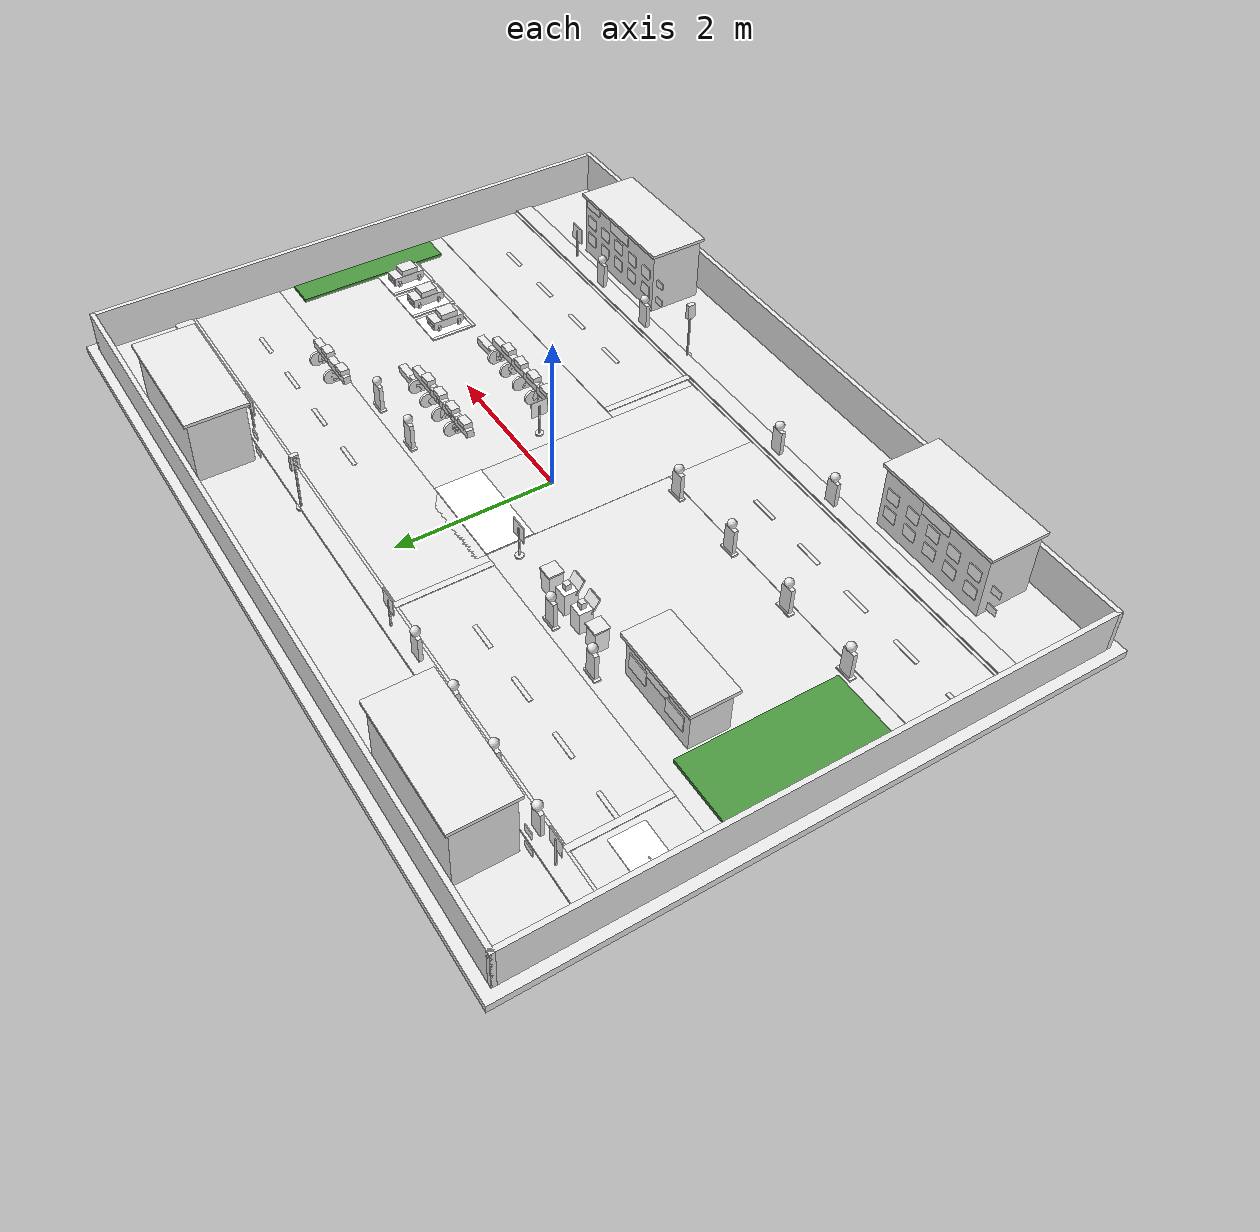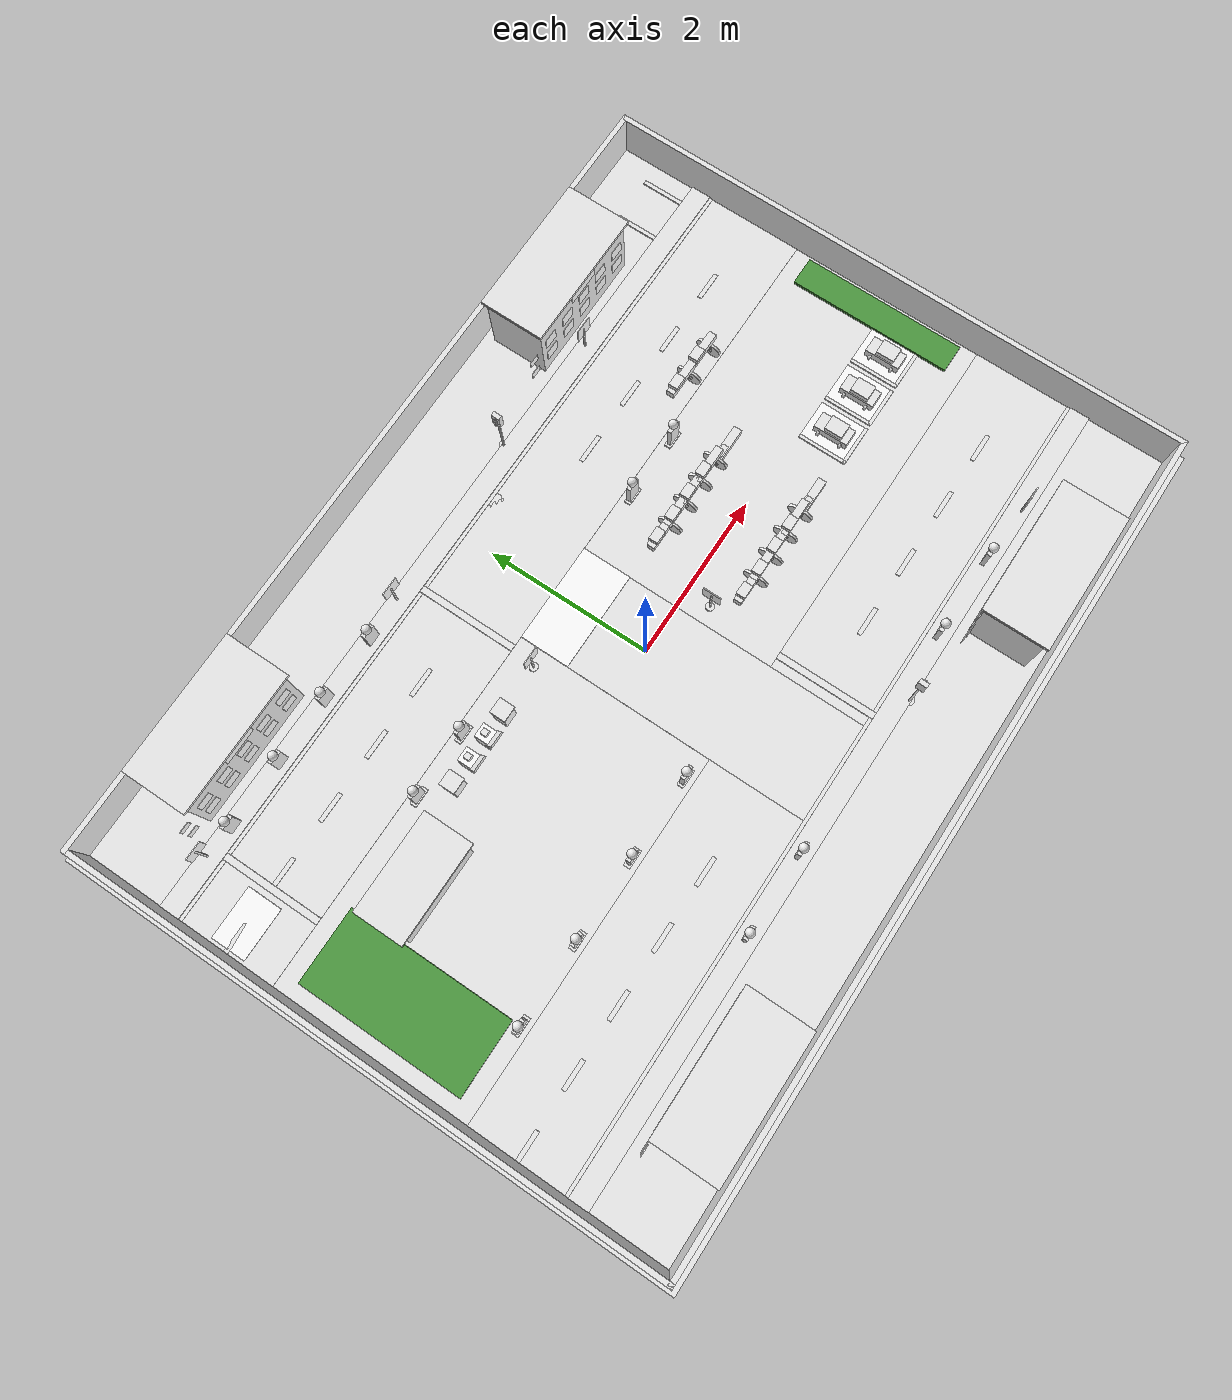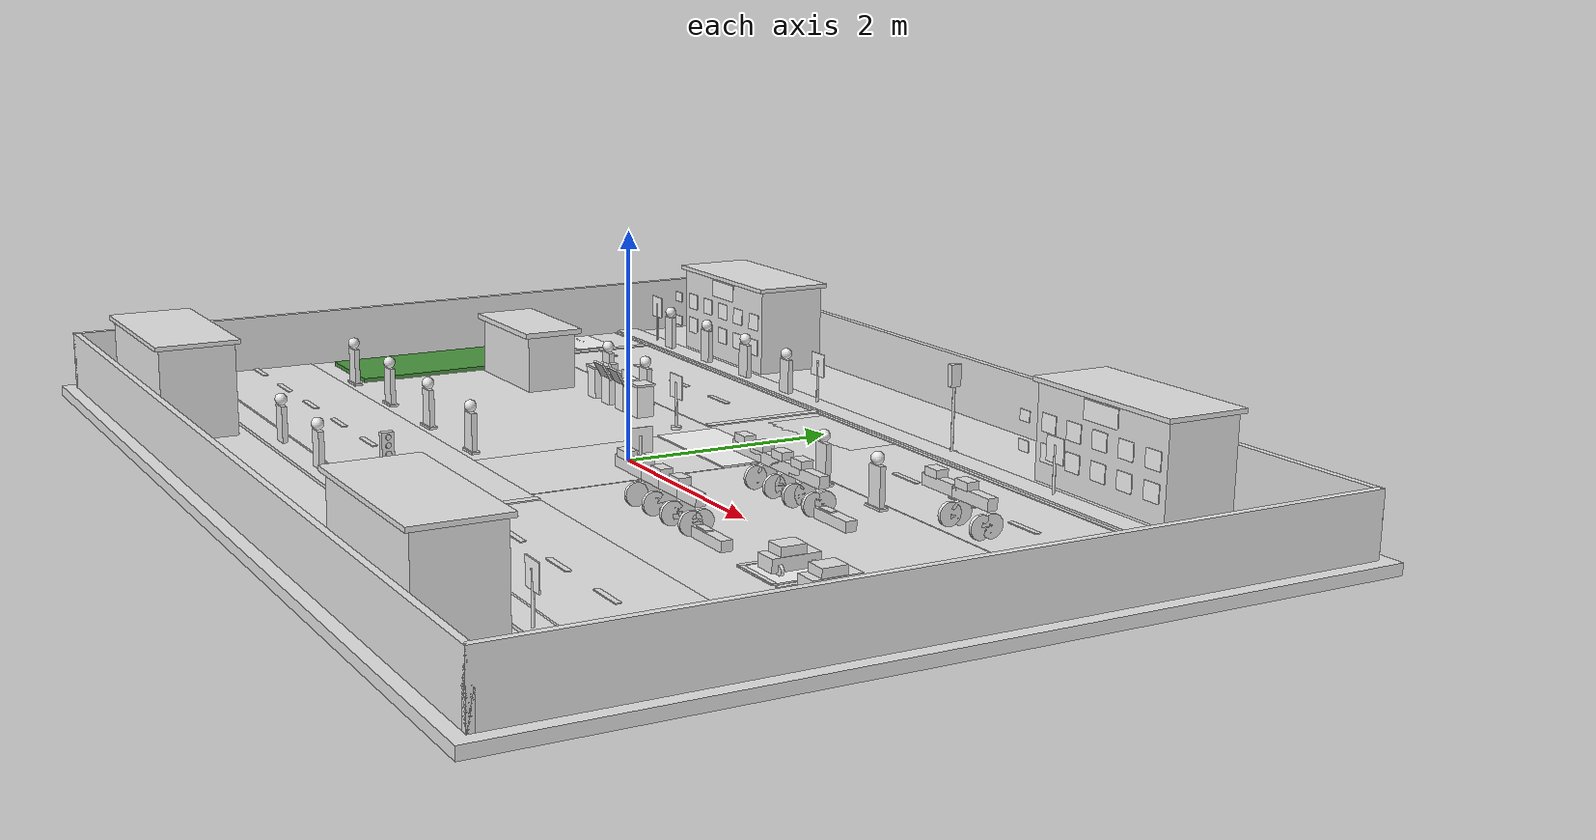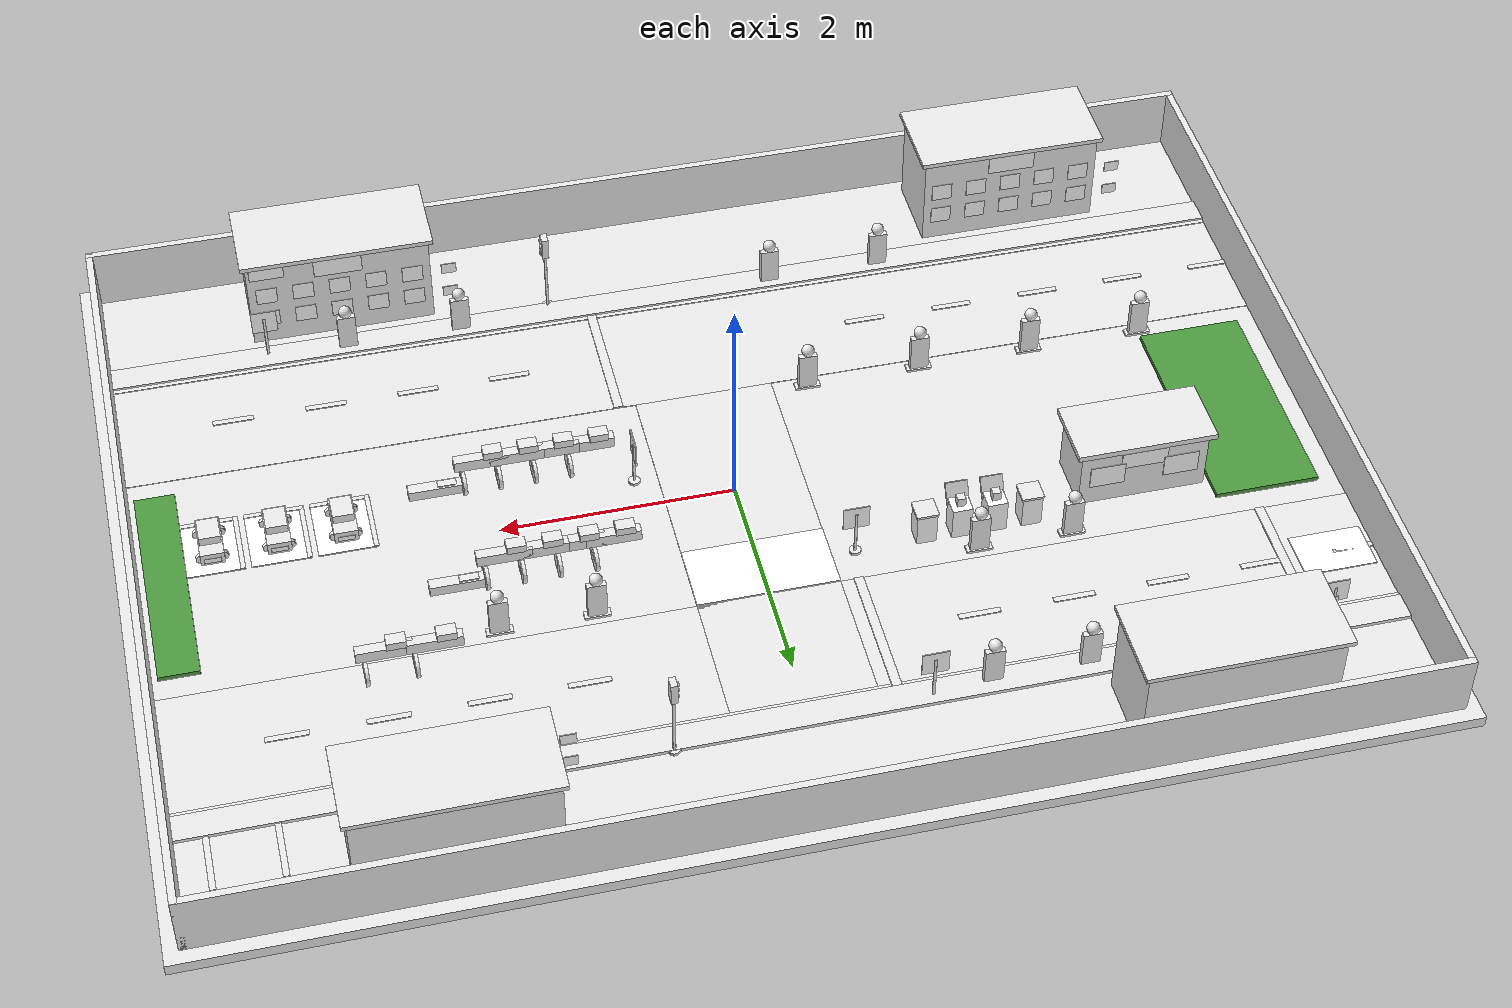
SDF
<?xml version="1.0" ?>
<sdf version="1.6">
  <world name="sq_community">
    <scene>
      <ambient>0.65 0.65 0.65 1</ambient>
      <background>0.72 0.78 0.85 1</background>
      <shadows>1</shadows>
      <grid>0</grid>
    </scene>
    <light name='sun' type='directional'>
      <cast_shadows>1</cast_shadows>
      <pose frame=''>0 0 12 0 -0 0</pose>
      <diffuse>0.95 0.95 0.92 1</diffuse>
      <specular>0.2 0.2 0.2 1</specular>
      <attenuation><range>1000</range><constant>0.9</constant>
        <linear>0.01</linear><quadratic>0.001</quadratic></attenuation>
      <direction>-0.4 0.3 -1</direction>
    </light>
    <light name='fill_n' type='point'>
      <pose frame=''>-2.0 2.0 2.2 0 -0 0</pose>
      <diffuse>0.5 0.5 0.5 1</diffuse><specular>0.1 0.1 0.1 1</specular>
      <attenuation><range>12</range><constant>0.6</constant>
        <linear>0.01</linear><quadratic>0.002</quadratic></attenuation>
      <cast_shadows>0</cast_shadows><direction>0 0 -1</direction>
    </light>
    <light name='fill_s' type='point'>
      <pose frame=''>2.5 -2.0 2.2 0 -0 0</pose>
      <diffuse>0.5 0.5 0.5 1</diffuse><specular>0.1 0.1 0.1 1</specular>
      <attenuation><range>12</range><constant>0.6</constant>
        <linear>0.01</linear><quadratic>0.002</quadratic></attenuation>
      <cast_shadows>0</cast_shadows><direction>0 0 -1</direction>
    </light>
    <light name='fill_c' type='point'>
      <pose frame=''>0.6 0.0 2.4 0 -0 0</pose>
      <diffuse>0.45 0.45 0.45 1</diffuse><specular>0.1 0.1 0.1 1</specular>
      <attenuation><range>12</range><constant>0.6</constant>
        <linear>0.01</linear><quadratic>0.002</quadratic></attenuation>
      <cast_shadows>0</cast_shadows><direction>0 0 -1</direction>
    </light>
    <gravity>0 0 -9.8</gravity>
    <magnetic_field>6e-06 2.3e-05 -4.2e-05</magnetic_field>
    <atmosphere type='adiabatic'/>
    <physics name='default_physics' default='0' type='ode'>
      <max_step_size>0.001</max_step_size>
      <real_time_factor>1</real_time_factor>
      <real_time_update_rate>1000</real_time_update_rate>
    </physics>
    <spherical_coordinates>
      <surface_model>EARTH_WGS84</surface_model>
      <latitude_deg>0</latitude_deg><longitude_deg>0</longitude_deg>
      <elevation>0</elevation><heading_deg>0</heading_deg>
    </spherical_coordinates>

    <!-- 红绿灯：先摆一盏红灯，运行期由 traffic_light_controller.py 动态换灯 -->
    <include>
      <uri>model://sq_traffic_light_red</uri>
      <pose>1.1 2.62 0 0 0 3.14159</pose>
      <name>sq_tl_1</name>
    </include>
    <include>
      <uri>model://sq_traffic_light_red</uri>
      <pose>1.1 -2.62 0 0 0 0</pose>
      <name>sq_tl_2</name>
    </include>

    <model name='sq_ground'>
      <static>1</static>
      <pose>0 0 0 0 0 0</pose>
      <link name='ground_base'><collision name='ground_base_c'><pose>0 0 -0.05 0 0 0</pose><geometry><box><size>10.3 7.5 0.1</size></box></geometry></collision><visual name='ground_base_v'><pose>0 0 -0.05 0 0 0</pose><geometry><box><size>10.3 7.5 0.1</size></box></geometry><material><script><uri>file://media/materials/scripts/gazebo.material</uri><name>Gazebo/White</name></script><ambient>0.132 0.1375 0.1485 1</ambient><diffuse>0.24 0.25 0.27 1</diffuse><specular>0.1 0.1 0.1 1</specular><emissive>0 0 0 1</emissive></material><cast_shadows>1</cast_shadows></visual></link>
      <link name='start_decal'><visual name='start_decal_v'><pose>-4.62 1.8 0.008 0 0 0</pose><geometry><box><size>0.62 0.42 0.012</size></box></geometry><material><script><uri>model://sq_textures/materials/scripts</uri><uri>model://sq_textures/materials/textures</uri><name>SQ_start_plate</name></script><ambient>1 1 1 1</ambient><diffuse>1 1 1 1</diffuse><specular>0.05 0.05 0.05 1</specular></material><cast_shadows>1</cast_shadows></visual></link>
      <link name='road_a'><visual name='road_a_v'><pose>0 1.8 0.002 0 0 0</pose><geometry><box><size>10 1.2 0.006</size></box></geometry><material><script><uri>file://media/materials/scripts/gazebo.material</uri><name>Gazebo/White</name></script><ambient>0.1815 0.187 0.198 1</ambient><diffuse>0.33 0.34 0.36 1</diffuse><specular>0.1 0.1 0.1 1</specular><emissive>0 0 0 1</emissive></material><cast_shadows>1</cast_shadows></visual></link>
      <link name='road_b'><visual name='road_b_v'><pose>0 -1.8 0.002 0 0 0</pose><geometry><box><size>10 1.2 0.006</size></box></geometry><material><script><uri>file://media/materials/scripts/gazebo.material</uri><name>Gazebo/White</name></script><ambient>0.1815 0.187 0.198 1</ambient><diffuse>0.33 0.34 0.36 1</diffuse><specular>0.1 0.1 0.1 1</specular><emissive>0 0 0 1</emissive></material><cast_shadows>1</cast_shadows></visual></link>
      <link name='road_c'><visual name='road_c_v'><pose>0 0 0.002 0 0 0</pose><geometry><box><size>1.2 4.8 0.006</size></box></geometry><material><script><uri>file://media/materials/scripts/gazebo.material</uri><name>Gazebo/White</name></script><ambient>0.1815 0.187 0.198 1</ambient><diffuse>0.33 0.34 0.36 1</diffuse><specular>0.1 0.1 0.1 1</specular><emissive>0 0 0 1</emissive></material><cast_shadows>1</cast_shadows></visual></link>
      <link name='grass_-4.35'><visual name='grass_-4.35_v'><pose>-4.35 0 0.02 0 0 0</pose><geometry><box><size>0.9 2 0.04</size></box></geometry><material><script><uri>model://sq_textures/materials/scripts</uri><uri>model://sq_textures/materials/textures</uri><name>SQ_gnd_grass</name></script><ambient>1 1 1 1</ambient><diffuse>1 1 1 1</diffuse><specular>0.05 0.05 0.05 1</specular></material><cast_shadows>1</cast_shadows></visual></link>
      <link name='grass_4.75'><visual name='grass_4.75_v'><pose>4.75 0 0.02 0 0 0</pose><geometry><box><size>0.34 2 0.04</size></box></geometry><material><script><uri>model://sq_textures/materials/scripts</uri><uri>model://sq_textures/materials/textures</uri><name>SQ_gnd_grass</name></script><ambient>1 1 1 1</ambient><diffuse>1 1 1 1</diffuse><specular>0.05 0.05 0.05 1</specular></material><cast_shadows>1</cast_shadows></visual></link>
      <link name='walk_2.5'><visual name='walk_2.5_v'><pose>0 2.52 0.015 0 0 0</pose><geometry><box><size>10 0.24 0.03</size></box></geometry><material><script><uri>file://media/materials/scripts/gazebo.material</uri><name>Gazebo/White</name></script><ambient>0.341 0.3355 0.319 1</ambient><diffuse>0.62 0.61 0.58 1</diffuse><specular>0.1 0.1 0.1 1</specular><emissive>0 0 0 1</emissive></material><cast_shadows>1</cast_shadows></visual></link>
      <link name='walk_-2.5'><visual name='walk_-2.5_v'><pose>0 -2.52 0.015 0 0 0</pose><geometry><box><size>10 0.24 0.03</size></box></geometry><material><script><uri>file://media/materials/scripts/gazebo.material</uri><name>Gazebo/White</name></script><ambient>0.341 0.3355 0.319 1</ambient><diffuse>0.62 0.61 0.58 1</diffuse><specular>0.1 0.1 0.1 1</specular><emissive>0 0 0 1</emissive></material><cast_shadows>1</cast_shadows></visual></link>
    </model>
    <model name='sq_markings'>
      <static>1</static>
      <pose>0 0 0 0 0 0</pose>
      <link name='dash_1.8_-4.80'><visual name='dash_1.8_-4.80_v'><pose>-4.8 1.8 0.008 0 0 0</pose><geometry><box><size>0.35 0.05 0.012</size></box></geometry><material><script><uri>file://media/materials/scripts/gazebo.material</uri><name>Gazebo/White</name></script><ambient>0.506 0.44 0.0825 1</ambient><diffuse>0.92 0.8 0.15 1</diffuse><specular>0.1 0.1 0.1 1</specular><emissive>0 0 0 1</emissive></material><cast_shadows>1</cast_shadows></visual></link>
      <link name='dash_1.8_-4.00'><visual name='dash_1.8_-4.00_v'><pose>-4 1.8 0.008 0 0 0</pose><geometry><box><size>0.35 0.05 0.012</size></box></geometry><material><script><uri>file://media/materials/scripts/gazebo.material</uri><name>Gazebo/White</name></script><ambient>0.506 0.44 0.0825 1</ambient><diffuse>0.92 0.8 0.15 1</diffuse><specular>0.1 0.1 0.1 1</specular><emissive>0 0 0 1</emissive></material><cast_shadows>1</cast_shadows></visual></link>
      <link name='dash_1.8_-3.20'><visual name='dash_1.8_-3.20_v'><pose>-3.2 1.8 0.008 0 0 0</pose><geometry><box><size>0.35 0.05 0.012</size></box></geometry><material><script><uri>file://media/materials/scripts/gazebo.material</uri><name>Gazebo/White</name></script><ambient>0.506 0.44 0.0825 1</ambient><diffuse>0.92 0.8 0.15 1</diffuse><specular>0.1 0.1 0.1 1</specular><emissive>0 0 0 1</emissive></material><cast_shadows>1</cast_shadows></visual></link>
      <link name='dash_1.8_-2.40'><visual name='dash_1.8_-2.40_v'><pose>-2.4 1.8 0.008 0 0 0</pose><geometry><box><size>0.35 0.05 0.012</size></box></geometry><material><script><uri>file://media/materials/scripts/gazebo.material</uri><name>Gazebo/White</name></script><ambient>0.506 0.44 0.0825 1</ambient><diffuse>0.92 0.8 0.15 1</diffuse><specular>0.1 0.1 0.1 1</specular><emissive>0 0 0 1</emissive></material><cast_shadows>1</cast_shadows></visual></link>
      <link name='dash_1.8_-1.60'><visual name='dash_1.8_-1.60_v'><pose>-1.6 1.8 0.008 0 0 0</pose><geometry><box><size>0.35 0.05 0.012</size></box></geometry><material><script><uri>file://media/materials/scripts/gazebo.material</uri><name>Gazebo/White</name></script><ambient>0.506 0.44 0.0825 1</ambient><diffuse>0.92 0.8 0.15 1</diffuse><specular>0.1 0.1 0.1 1</specular><emissive>0 0 0 1</emissive></material><cast_shadows>1</cast_shadows></visual></link>
      <link name='dash_1.8_1.60'><visual name='dash_1.8_1.60_v'><pose>1.6 1.8 0.008 0 0 0</pose><geometry><box><size>0.35 0.05 0.012</size></box></geometry><material><script><uri>file://media/materials/scripts/gazebo.material</uri><name>Gazebo/White</name></script><ambient>0.506 0.44 0.0825 1</ambient><diffuse>0.92 0.8 0.15 1</diffuse><specular>0.1 0.1 0.1 1</specular><emissive>0 0 0 1</emissive></material><cast_shadows>1</cast_shadows></visual></link>
      <link name='dash_1.8_2.40'><visual name='dash_1.8_2.40_v'><pose>2.4 1.8 0.008 0 0 0</pose><geometry><box><size>0.35 0.05 0.012</size></box></geometry><material><script><uri>file://media/materials/scripts/gazebo.material</uri><name>Gazebo/White</name></script><ambient>0.506 0.44 0.0825 1</ambient><diffuse>0.92 0.8 0.15 1</diffuse><specular>0.1 0.1 0.1 1</specular><emissive>0 0 0 1</emissive></material><cast_shadows>1</cast_shadows></visual></link>
      <link name='dash_1.8_3.20'><visual name='dash_1.8_3.20_v'><pose>3.2 1.8 0.008 0 0 0</pose><geometry><box><size>0.35 0.05 0.012</size></box></geometry><material><script><uri>file://media/materials/scripts/gazebo.material</uri><name>Gazebo/White</name></script><ambient>0.506 0.44 0.0825 1</ambient><diffuse>0.92 0.8 0.15 1</diffuse><specular>0.1 0.1 0.1 1</specular><emissive>0 0 0 1</emissive></material><cast_shadows>1</cast_shadows></visual></link>
      <link name='dash_1.8_4.00'><visual name='dash_1.8_4.00_v'><pose>4 1.8 0.008 0 0 0</pose><geometry><box><size>0.35 0.05 0.012</size></box></geometry><material><script><uri>file://media/materials/scripts/gazebo.material</uri><name>Gazebo/White</name></script><ambient>0.506 0.44 0.0825 1</ambient><diffuse>0.92 0.8 0.15 1</diffuse><specular>0.1 0.1 0.1 1</specular><emissive>0 0 0 1</emissive></material><cast_shadows>1</cast_shadows></visual></link>
      <link name='dash_-1.8_-4.80'><visual name='dash_-1.8_-4.80_v'><pose>-4.8 -1.8 0.008 0 0 0</pose><geometry><box><size>0.35 0.05 0.012</size></box></geometry><material><script><uri>file://media/materials/scripts/gazebo.material</uri><name>Gazebo/White</name></script><ambient>0.506 0.44 0.0825 1</ambient><diffuse>0.92 0.8 0.15 1</diffuse><specular>0.1 0.1 0.1 1</specular><emissive>0 0 0 1</emissive></material><cast_shadows>1</cast_shadows></visual></link>
      <link name='dash_-1.8_-4.00'><visual name='dash_-1.8_-4.00_v'><pose>-4 -1.8 0.008 0 0 0</pose><geometry><box><size>0.35 0.05 0.012</size></box></geometry><material><script><uri>file://media/materials/scripts/gazebo.material</uri><name>Gazebo/White</name></script><ambient>0.506 0.44 0.0825 1</ambient><diffuse>0.92 0.8 0.15 1</diffuse><specular>0.1 0.1 0.1 1</specular><emissive>0 0 0 1</emissive></material><cast_shadows>1</cast_shadows></visual></link>
      <link name='dash_-1.8_-3.20'><visual name='dash_-1.8_-3.20_v'><pose>-3.2 -1.8 0.008 0 0 0</pose><geometry><box><size>0.35 0.05 0.012</size></box></geometry><material><script><uri>file://media/materials/scripts/gazebo.material</uri><name>Gazebo/White</name></script><ambient>0.506 0.44 0.0825 1</ambient><diffuse>0.92 0.8 0.15 1</diffuse><specular>0.1 0.1 0.1 1</specular><emissive>0 0 0 1</emissive></material><cast_shadows>1</cast_shadows></visual></link>
      <link name='dash_-1.8_-2.40'><visual name='dash_-1.8_-2.40_v'><pose>-2.4 -1.8 0.008 0 0 0</pose><geometry><box><size>0.35 0.05 0.012</size></box></geometry><material><script><uri>file://media/materials/scripts/gazebo.material</uri><name>Gazebo/White</name></script><ambient>0.506 0.44 0.0825 1</ambient><diffuse>0.92 0.8 0.15 1</diffuse><specular>0.1 0.1 0.1 1</specular><emissive>0 0 0 1</emissive></material><cast_shadows>1</cast_shadows></visual></link>
      <link name='dash_-1.8_-1.60'><visual name='dash_-1.8_-1.60_v'><pose>-1.6 -1.8 0.008 0 0 0</pose><geometry><box><size>0.35 0.05 0.012</size></box></geometry><material><script><uri>file://media/materials/scripts/gazebo.material</uri><name>Gazebo/White</name></script><ambient>0.506 0.44 0.0825 1</ambient><diffuse>0.92 0.8 0.15 1</diffuse><specular>0.1 0.1 0.1 1</specular><emissive>0 0 0 1</emissive></material><cast_shadows>1</cast_shadows></visual></link>
      <link name='dash_-1.8_1.60'><visual name='dash_-1.8_1.60_v'><pose>1.6 -1.8 0.008 0 0 0</pose><geometry><box><size>0.35 0.05 0.012</size></box></geometry><material><script><uri>file://media/materials/scripts/gazebo.material</uri><name>Gazebo/White</name></script><ambient>0.506 0.44 0.0825 1</ambient><diffuse>0.92 0.8 0.15 1</diffuse><specular>0.1 0.1 0.1 1</specular><emissive>0 0 0 1</emissive></material><cast_shadows>1</cast_shadows></visual></link>
      <link name='dash_-1.8_2.40'><visual name='dash_-1.8_2.40_v'><pose>2.4 -1.8 0.008 0 0 0</pose><geometry><box><size>0.35 0.05 0.012</size></box></geometry><material><script><uri>file://media/materials/scripts/gazebo.material</uri><name>Gazebo/White</name></script><ambient>0.506 0.44 0.0825 1</ambient><diffuse>0.92 0.8 0.15 1</diffuse><specular>0.1 0.1 0.1 1</specular><emissive>0 0 0 1</emissive></material><cast_shadows>1</cast_shadows></visual></link>
      <link name='dash_-1.8_3.20'><visual name='dash_-1.8_3.20_v'><pose>3.2 -1.8 0.008 0 0 0</pose><geometry><box><size>0.35 0.05 0.012</size></box></geometry><material><script><uri>file://media/materials/scripts/gazebo.material</uri><name>Gazebo/White</name></script><ambient>0.506 0.44 0.0825 1</ambient><diffuse>0.92 0.8 0.15 1</diffuse><specular>0.1 0.1 0.1 1</specular><emissive>0 0 0 1</emissive></material><cast_shadows>1</cast_shadows></visual></link>
      <link name='dash_-1.8_4.00'><visual name='dash_-1.8_4.00_v'><pose>4 -1.8 0.008 0 0 0</pose><geometry><box><size>0.35 0.05 0.012</size></box></geometry><material><script><uri>file://media/materials/scripts/gazebo.material</uri><name>Gazebo/White</name></script><ambient>0.506 0.44 0.0825 1</ambient><diffuse>0.92 0.8 0.15 1</diffuse><specular>0.1 0.1 0.1 1</specular><emissive>0 0 0 1</emissive></material><cast_shadows>1</cast_shadows></visual></link>
      <link name='edge_1.8'><visual name='edge_1.8_v'><pose>0 2.38 0.007 0 0 0</pose><geometry><box><size>10 0.04 0.01</size></box></geometry><material><script><uri>file://media/materials/scripts/gazebo.material</uri><name>Gazebo/White</name></script><ambient>0.5225 0.5225 0.5225 1</ambient><diffuse>0.95 0.95 0.95 1</diffuse><specular>0.1 0.1 0.1 1</specular><emissive>0 0 0 1</emissive></material><cast_shadows>1</cast_shadows></visual></link>
      <link name='edge_-1.8'><visual name='edge_-1.8_v'><pose>0 -2.38 0.007 0 0 0</pose><geometry><box><size>10 0.04 0.01</size></box></geometry><material><script><uri>file://media/materials/scripts/gazebo.material</uri><name>Gazebo/White</name></script><ambient>0.5225 0.5225 0.5225 1</ambient><diffuse>0.95 0.95 0.95 1</diffuse><specular>0.1 0.1 0.1 1</specular><emissive>0 0 0 1</emissive></material><cast_shadows>1</cast_shadows></visual></link>
      <link name='start_line'><visual name='start_line_v'><pose>-4.2 1.8 0.009 0 0 0</pose><geometry><box><size>0.08 1.2 0.014</size></box></geometry><material><script><uri>file://media/materials/scripts/gazebo.material</uri><name>Gazebo/White</name></script><ambient>0.5225 0.5225 0.5225 1</ambient><diffuse>0.95 0.95 0.95 1</diffuse><specular>0.1 0.1 0.1 1</specular><emissive>0 0 0 1</emissive></material><cast_shadows>1</cast_shadows></visual></link>
      <link name='wait_a'><visual name='wait_a_v'><pose>-0.75 1.8 0.009 0 0 0</pose><geometry><box><size>0.08 1.2 0.014</size></box></geometry><material><script><uri>file://media/materials/scripts/gazebo.material</uri><name>Gazebo/White</name></script><ambient>0.5225 0.5225 0.5225 1</ambient><diffuse>0.95 0.95 0.95 1</diffuse><specular>0.1 0.1 0.1 1</specular><emissive>0 0 0 1</emissive></material><cast_shadows>1</cast_shadows></visual></link>
      <link name='wait_b'><visual name='wait_b_v'><pose>0.75 -1.8 0.009 0 0 0</pose><geometry><box><size>0.08 1.2 0.014</size></box></geometry><material><script><uri>file://media/materials/scripts/gazebo.material</uri><name>Gazebo/White</name></script><ambient>0.5225 0.5225 0.5225 1</ambient><diffuse>0.95 0.95 0.95 1</diffuse><specular>0.1 0.1 0.1 1</specular><emissive>0 0 0 1</emissive></material><cast_shadows>1</cast_shadows></visual></link>
      <link name='crosswalk'><visual name='crosswalk_v'><pose>0 0.9 0.01 0 0 0</pose><geometry><box><size>1.2 0.6 0.016</size></box></geometry><material><script><uri>model://sq_textures/materials/scripts</uri><uri>model://sq_textures/materials/textures</uri><name>SQ_gnd_crosswalk</name></script><ambient>1 1 1 1</ambient><diffuse>1 1 1 1</diffuse><specular>0.05 0.05 0.05 1</specular></material><cast_shadows>1</cast_shadows></visual></link>
      <link name='bay_0_g'><visual name='bay_0_g_v'><pose>3.25 -0.35 0.005 0 0 0</pose><geometry><box><size>0.5 0.6 0.01</size></box></geometry><material><script><uri>model://sq_textures/materials/scripts</uri><uri>model://sq_textures/materials/textures</uri><name>SQ_gnd_parking</name></script><ambient>1 1 1 1</ambient><diffuse>1 1 1 1</diffuse><specular>0.05 0.05 0.05 1</specular></material><cast_shadows>1</cast_shadows></visual></link>
      <link name='bay_0_fl'><visual name='bay_0_fl_v'><pose>3.02 -0.35 0.009 0 0 0</pose><geometry><box><size>0.04 0.6 0.014</size></box></geometry><material><script><uri>file://media/materials/scripts/gazebo.material</uri><name>Gazebo/White</name></script><ambient>0.5225 0.5225 0.5225 1</ambient><diffuse>0.95 0.95 0.95 1</diffuse><specular>0.1 0.1 0.1 1</specular><emissive>0 0 0 1</emissive></material><cast_shadows>1</cast_shadows></visual></link>
      <link name='bay_0_bk'><visual name='bay_0_bk_v'><pose>3.25 -0.63 0.009 0 0 0</pose><geometry><box><size>0.5 0.04 0.014</size></box></geometry><material><script><uri>file://media/materials/scripts/gazebo.material</uri><name>Gazebo/White</name></script><ambient>0.5225 0.5225 0.5225 1</ambient><diffuse>0.95 0.95 0.95 1</diffuse><specular>0.1 0.1 0.1 1</specular><emissive>0 0 0 1</emissive></material><cast_shadows>1</cast_shadows></visual></link>
      <link name='bay_1_g'><visual name='bay_1_g_v'><pose>3.8 -0.35 0.005 0 0 0</pose><geometry><box><size>0.5 0.6 0.01</size></box></geometry><material><script><uri>model://sq_textures/materials/scripts</uri><uri>model://sq_textures/materials/textures</uri><name>SQ_gnd_parking</name></script><ambient>1 1 1 1</ambient><diffuse>1 1 1 1</diffuse><specular>0.05 0.05 0.05 1</specular></material><cast_shadows>1</cast_shadows></visual></link>
      <link name='bay_1_fl'><visual name='bay_1_fl_v'><pose>3.57 -0.35 0.009 0 0 0</pose><geometry><box><size>0.04 0.6 0.014</size></box></geometry><material><script><uri>file://media/materials/scripts/gazebo.material</uri><name>Gazebo/White</name></script><ambient>0.5225 0.5225 0.5225 1</ambient><diffuse>0.95 0.95 0.95 1</diffuse><specular>0.1 0.1 0.1 1</specular><emissive>0 0 0 1</emissive></material><cast_shadows>1</cast_shadows></visual></link>
      <link name='bay_1_bk'><visual name='bay_1_bk_v'><pose>3.8 -0.63 0.009 0 0 0</pose><geometry><box><size>0.5 0.04 0.014</size></box></geometry><material><script><uri>file://media/materials/scripts/gazebo.material</uri><name>Gazebo/White</name></script><ambient>0.5225 0.5225 0.5225 1</ambient><diffuse>0.95 0.95 0.95 1</diffuse><specular>0.1 0.1 0.1 1</specular><emissive>0 0 0 1</emissive></material><cast_shadows>1</cast_shadows></visual></link>
      <link name='bay_2_g'><visual name='bay_2_g_v'><pose>4.35 -0.35 0.005 0 0 0</pose><geometry><box><size>0.5 0.6 0.01</size></box></geometry><material><script><uri>model://sq_textures/materials/scripts</uri><uri>model://sq_textures/materials/textures</uri><name>SQ_gnd_parking</name></script><ambient>1 1 1 1</ambient><diffuse>1 1 1 1</diffuse><specular>0.05 0.05 0.05 1</specular></material><cast_shadows>1</cast_shadows></visual></link>
      <link name='bay_2_fl'><visual name='bay_2_fl_v'><pose>4.12 -0.35 0.009 0 0 0</pose><geometry><box><size>0.04 0.6 0.014</size></box></geometry><material><script><uri>file://media/materials/scripts/gazebo.material</uri><name>Gazebo/White</name></script><ambient>0.5225 0.5225 0.5225 1</ambient><diffuse>0.95 0.95 0.95 1</diffuse><specular>0.1 0.1 0.1 1</specular><emissive>0 0 0 1</emissive></material><cast_shadows>1</cast_shadows></visual></link>
      <link name='bay_2_bk'><visual name='bay_2_bk_v'><pose>4.35 -0.63 0.009 0 0 0</pose><geometry><box><size>0.5 0.04 0.014</size></box></geometry><material><script><uri>file://media/materials/scripts/gazebo.material</uri><name>Gazebo/White</name></script><ambient>0.5225 0.5225 0.5225 1</ambient><diffuse>0.95 0.95 0.95 1</diffuse><specular>0.1 0.1 0.1 1</specular><emissive>0 0 0 1</emissive></material><cast_shadows>1</cast_shadows></visual></link>
      <link name='slot_-0.28_0.00'><visual name='slot_-0.28_0.00_v'><pose>4.175 2.8 0.009 0 0 0</pose><geometry><box><size>0.05 0.7 0.014</size></box></geometry><material><script><uri>file://media/materials/scripts/gazebo.material</uri><name>Gazebo/White</name></script><ambient>0.5225 0.5225 0.5225 1</ambient><diffuse>0.95 0.95 0.95 1</diffuse><specular>0.1 0.1 0.1 1</specular><emissive>0 0 0 1</emissive></material><cast_shadows>1</cast_shadows></visual></link>
      <link name='slot_0.28_0.00'><visual name='slot_0.28_0.00_v'><pose>4.725 2.8 0.009 0 0 0</pose><geometry><box><size>0.05 0.7 0.014</size></box></geometry><material><script><uri>file://media/materials/scripts/gazebo.material</uri><name>Gazebo/White</name></script><ambient>0.5225 0.5225 0.5225 1</ambient><diffuse>0.95 0.95 0.95 1</diffuse><specular>0.1 0.1 0.1 1</specular><emissive>0 0 0 1</emissive></material><cast_shadows>1</cast_shadows></visual></link>
      <link name='slot_0.00_-0.35'><visual name='slot_0.00_-0.35_v'><pose>4.45 2.45 0.009 0 0 0</pose><geometry><box><size>0.55 0.05 0.014</size></box></geometry><material><script><uri>file://media/materials/scripts/gazebo.material</uri><name>Gazebo/White</name></script><ambient>0.5225 0.5225 0.5225 1</ambient><diffuse>0.95 0.95 0.95 1</diffuse><specular>0.1 0.1 0.1 1</specular><emissive>0 0 0 1</emissive></material><cast_shadows>1</cast_shadows></visual></link>
    </model>
    <model name='sq_walls'>
      <static>1</static>
      <pose>0 0 0 0 0 0</pose>
      <link name='wall_n'><collision name='wall_n_c'><pose>0 3.6 0.275 0 0 0</pose><geometry><box><size>10.06 0.06 0.55</size></box></geometry></collision><visual name='wall_n_v'><pose>0 3.6 0.275 0 0 0</pose><geometry><box><size>10.06 0.06 0.55</size></box></geometry><material><script><uri>file://media/materials/scripts/gazebo.material</uri><name>Gazebo/White</name></script><ambient>0.3025 0.3025 0.319 1</ambient><diffuse>0.55 0.55 0.58 1</diffuse><specular>0.1 0.1 0.1 1</specular><emissive>0 0 0 1</emissive></material><cast_shadows>1</cast_shadows></visual></link>
      <link name='wall_s'><collision name='wall_s_c'><pose>0 -3.6 0.275 0 0 0</pose><geometry><box><size>10.06 0.06 0.55</size></box></geometry></collision><visual name='wall_s_v'><pose>0 -3.6 0.275 0 0 0</pose><geometry><box><size>10.06 0.06 0.55</size></box></geometry><material><script><uri>file://media/materials/scripts/gazebo.material</uri><name>Gazebo/White</name></script><ambient>0.3025 0.3025 0.319 1</ambient><diffuse>0.55 0.55 0.58 1</diffuse><specular>0.1 0.1 0.1 1</specular><emissive>0 0 0 1</emissive></material><cast_shadows>1</cast_shadows></visual></link>
      <link name='wall_w'><collision name='wall_w_c'><pose>-5 0 0.275 0 0 0</pose><geometry><box><size>0.06 7.26 0.55</size></box></geometry></collision><visual name='wall_w_v'><pose>-5 0 0.275 0 0 0</pose><geometry><box><size>0.06 7.26 0.55</size></box></geometry><material><script><uri>file://media/materials/scripts/gazebo.material</uri><name>Gazebo/White</name></script><ambient>0.3025 0.3025 0.319 1</ambient><diffuse>0.55 0.55 0.58 1</diffuse><specular>0.1 0.1 0.1 1</specular><emissive>0 0 0 1</emissive></material><cast_shadows>1</cast_shadows></visual></link>
      <link name='wall_e'><collision name='wall_e_c'><pose>5 0 0.275 0 0 0</pose><geometry><box><size>0.06 7.26 0.55</size></box></geometry></collision><visual name='wall_e_v'><pose>5 0 0.275 0 0 0</pose><geometry><box><size>0.06 7.26 0.55</size></box></geometry><material><script><uri>file://media/materials/scripts/gazebo.material</uri><name>Gazebo/White</name></script><ambient>0.3025 0.3025 0.319 1</ambient><diffuse>0.55 0.55 0.58 1</diffuse><specular>0.1 0.1 0.1 1</specular><emissive>0 0 0 1</emissive></material><cast_shadows>1</cast_shadows></visual></link>
    </model>
    <model name='sq_buildings'>
      <static>1</static>
      <pose>0 0 0 0 0 0</pose>
      <link name='bld_A_body'><collision name='bld_A_body_c'><pose>-3.2 3.1 0.425 0 0 0</pose><geometry><box><size>1.6 0.7 0.85</size></box></geometry></collision><visual name='bld_A_body_v'><pose>-3.2 3.1 0.425 0 0 0</pose><geometry><box><size>1.6 0.7 0.85</size></box></geometry><material><script><uri>file://media/materials/scripts/gazebo.material</uri><name>Gazebo/White</name></script><ambient>0.407 0.396 0.374 1</ambient><diffuse>0.74 0.72 0.68 1</diffuse><specular>0.1 0.1 0.1 1</specular><emissive>0 0 0 1</emissive></material><cast_shadows>1</cast_shadows></visual></link>
      <link name='bld_A_win0'><collision name='bld_A_win0_c'><pose>-3.84 2.746 0.26 0 0 0</pose><geometry><box><size>0.18 0.008 0.16</size></box></geometry></collision><visual name='bld_A_win0_v'><pose>-3.84 2.746 0.26 0 0 0</pose><geometry><box><size>0.18 0.008 0.16</size></box></geometry><material><script><uri>model://sq_textures/materials/scripts</uri><uri>model://sq_textures/materials/textures</uri><name>SQ_win_fire</name></script><ambient>1 1 1 1</ambient><diffuse>1 1 1 1</diffuse><specular>0.05 0.05 0.05 1</specular></material><cast_shadows>1</cast_shadows></visual></link>
      <link name='bld_A_win1'><collision name='bld_A_win1_c'><pose>-3.52 2.746 0.26 0 0 0</pose><geometry><box><size>0.18 0.008 0.16</size></box></geometry></collision><visual name='bld_A_win1_v'><pose>-3.52 2.746 0.26 0 0 0</pose><geometry><box><size>0.18 0.008 0.16</size></box></geometry><material><script><uri>model://sq_textures/materials/scripts</uri><uri>model://sq_textures/materials/textures</uri><name>SQ_win_normal</name></script><ambient>1 1 1 1</ambient><diffuse>1 1 1 1</diffuse><specular>0.05 0.05 0.05 1</specular></material><cast_shadows>1</cast_shadows></visual></link>
      <link name='bld_A_win2'><collision name='bld_A_win2_c'><pose>-3.2 2.746 0.26 0 0 0</pose><geometry><box><size>0.18 0.008 0.16</size></box></geometry></collision><visual name='bld_A_win2_v'><pose>-3.2 2.746 0.26 0 0 0</pose><geometry><box><size>0.18 0.008 0.16</size></box></geometry><material><script><uri>model://sq_textures/materials/scripts</uri><uri>model://sq_textures/materials/textures</uri><name>SQ_win_normal</name></script><ambient>1 1 1 1</ambient><diffuse>1 1 1 1</diffuse><specular>0.05 0.05 0.05 1</specular></material><cast_shadows>1</cast_shadows></visual></link>
      <link name='bld_A_win3'><collision name='bld_A_win3_c'><pose>-2.88 2.746 0.26 0 0 0</pose><geometry><box><size>0.18 0.008 0.16</size></box></geometry></collision><visual name='bld_A_win3_v'><pose>-2.88 2.746 0.26 0 0 0</pose><geometry><box><size>0.18 0.008 0.16</size></box></geometry><material><script><uri>model://sq_textures/materials/scripts</uri><uri>model://sq_textures/materials/textures</uri><name>SQ_win_fire</name></script><ambient>1 1 1 1</ambient><diffuse>1 1 1 1</diffuse><specular>0.05 0.05 0.05 1</specular></material><cast_shadows>1</cast_shadows></visual></link>
      <link name='bld_A_win4'><collision name='bld_A_win4_c'><pose>-2.56 2.746 0.26 0 0 0</pose><geometry><box><size>0.18 0.008 0.16</size></box></geometry></collision><visual name='bld_A_win4_v'><pose>-2.56 2.746 0.26 0 0 0</pose><geometry><box><size>0.18 0.008 0.16</size></box></geometry><material><script><uri>model://sq_textures/materials/scripts</uri><uri>model://sq_textures/materials/textures</uri><name>SQ_win_normal</name></script><ambient>1 1 1 1</ambient><diffuse>1 1 1 1</diffuse><specular>0.05 0.05 0.05 1</specular></material><cast_shadows>1</cast_shadows></visual></link>
      <link name='bld_A_win5'><collision name='bld_A_win5_c'><pose>-3.84 2.746 0.52 0 0 0</pose><geometry><box><size>0.18 0.008 0.16</size></box></geometry></collision><visual name='bld_A_win5_v'><pose>-3.84 2.746 0.52 0 0 0</pose><geometry><box><size>0.18 0.008 0.16</size></box></geometry><material><script><uri>model://sq_textures/materials/scripts</uri><uri>model://sq_textures/materials/textures</uri><name>SQ_win_normal</name></script><ambient>1 1 1 1</ambient><diffuse>1 1 1 1</diffuse><specular>0.05 0.05 0.05 1</specular></material><cast_shadows>1</cast_shadows></visual></link>
      <link name='bld_A_win6'><collision name='bld_A_win6_c'><pose>-3.52 2.746 0.52 0 0 0</pose><geometry><box><size>0.18 0.008 0.16</size></box></geometry></collision><visual name='bld_A_win6_v'><pose>-3.52 2.746 0.52 0 0 0</pose><geometry><box><size>0.18 0.008 0.16</size></box></geometry><material><script><uri>model://sq_textures/materials/scripts</uri><uri>model://sq_textures/materials/textures</uri><name>SQ_win_fire</name></script><ambient>1 1 1 1</ambient><diffuse>1 1 1 1</diffuse><specular>0.05 0.05 0.05 1</specular></material><cast_shadows>1</cast_shadows></visual></link>
      <link name='bld_A_win7'><collision name='bld_A_win7_c'><pose>-3.2 2.746 0.52 0 0 0</pose><geometry><box><size>0.18 0.008 0.16</size></box></geometry></collision><visual name='bld_A_win7_v'><pose>-3.2 2.746 0.52 0 0 0</pose><geometry><box><size>0.18 0.008 0.16</size></box></geometry><material><script><uri>model://sq_textures/materials/scripts</uri><uri>model://sq_textures/materials/textures</uri><name>SQ_win_normal</name></script><ambient>1 1 1 1</ambient><diffuse>1 1 1 1</diffuse><specular>0.05 0.05 0.05 1</specular></material><cast_shadows>1</cast_shadows></visual></link>
      <link name='bld_A_win8'><collision name='bld_A_win8_c'><pose>-2.88 2.746 0.52 0 0 0</pose><geometry><box><size>0.18 0.008 0.16</size></box></geometry></collision><visual name='bld_A_win8_v'><pose>-2.88 2.746 0.52 0 0 0</pose><geometry><box><size>0.18 0.008 0.16</size></box></geometry><material><script><uri>model://sq_textures/materials/scripts</uri><uri>model://sq_textures/materials/textures</uri><name>SQ_win_normal</name></script><ambient>1 1 1 1</ambient><diffuse>1 1 1 1</diffuse><specular>0.05 0.05 0.05 1</specular></material><cast_shadows>1</cast_shadows></visual></link>
      <link name='bld_A_win9'><collision name='bld_A_win9_c'><pose>-2.56 2.746 0.52 0 0 0</pose><geometry><box><size>0.18 0.008 0.16</size></box></geometry></collision><visual name='bld_A_win9_v'><pose>-2.56 2.746 0.52 0 0 0</pose><geometry><box><size>0.18 0.008 0.16</size></box></geometry><material><script><uri>model://sq_textures/materials/scripts</uri><uri>model://sq_textures/materials/textures</uri><name>SQ_win_normal</name></script><ambient>1 1 1 1</ambient><diffuse>1 1 1 1</diffuse><specular>0.05 0.05 0.05 1</specular></material><cast_shadows>1</cast_shadows></visual></link>
      <link name='bld_A_fl0'><collision name='bld_A_fl0_c'><pose>-4.16 2.746 0.26 0 0 0</pose><geometry><box><size>0.13 0.008 0.1</size></box></geometry></collision><visual name='bld_A_fl0_v'><pose>-4.16 2.746 0.26 0 0 0</pose><geometry><box><size>0.13 0.008 0.1</size></box></geometry><material><script><uri>model://sq_textures/materials/scripts</uri><uri>model://sq_textures/materials/textures</uri><name>SQ_floor_1f</name></script><ambient>1 1 1 1</ambient><diffuse>1 1 1 1</diffuse><specular>0.05 0.05 0.05 1</specular></material><cast_shadows>1</cast_shadows></visual></link>
      <link name='bld_A_fl1'><collision name='bld_A_fl1_c'><pose>-4.16 2.746 0.52 0 0 0</pose><geometry><box><size>0.13 0.008 0.1</size></box></geometry></collision><visual name='bld_A_fl1_v'><pose>-4.16 2.746 0.52 0 0 0</pose><geometry><box><size>0.13 0.008 0.1</size></box></geometry><material><script><uri>model://sq_textures/materials/scripts</uri><uri>model://sq_textures/materials/textures</uri><name>SQ_floor_2f</name></script><ambient>1 1 1 1</ambient><diffuse>1 1 1 1</diffuse><specular>0.05 0.05 0.05 1</specular></material><cast_shadows>1</cast_shadows></visual></link>
      <link name='bld_A_plate'><collision name='bld_A_plate_c'><pose>-3.2 2.746 0.74 0 0 0</pose><geometry><box><size>0.42 0.008 0.17</size></box></geometry></collision><visual name='bld_A_plate_v'><pose>-3.2 2.746 0.74 0 0 0</pose><geometry><box><size>0.42 0.008 0.17</size></box></geometry><material><script><uri>model://sq_textures/materials/scripts</uri><uri>model://sq_textures/materials/textures</uri><name>SQ_bldg_A</name></script><ambient>1 1 1 1</ambient><diffuse>1 1 1 1</diffuse><specular>0.05 0.05 0.05 1</specular></material><cast_shadows>1</cast_shadows></visual></link>
      <link name='bld_A_roof'><visual name='bld_A_roof_v'><pose>-3.2 3.1 0.87 0 0 0</pose><geometry><box><size>1.68 0.78 0.04</size></box></geometry><material><script><uri>file://media/materials/scripts/gazebo.material</uri><name>Gazebo/White</name></script><ambient>0.2475 0.242 0.253 1</ambient><diffuse>0.45 0.44 0.46 1</diffuse><specular>0.1 0.1 0.1 1</specular><emissive>0 0 0 1</emissive></material><cast_shadows>1</cast_shadows></visual></link>
      <link name='bld_B_body'><collision name='bld_B_body_c'><pose>2.9 3.1 0.425 0 0 0</pose><geometry><box><size>1.6 0.7 0.85</size></box></geometry></collision><visual name='bld_B_body_v'><pose>2.9 3.1 0.425 0 0 0</pose><geometry><box><size>1.6 0.7 0.85</size></box></geometry><material><script><uri>file://media/materials/scripts/gazebo.material</uri><name>Gazebo/White</name></script><ambient>0.407 0.396 0.374 1</ambient><diffuse>0.74 0.72 0.68 1</diffuse><specular>0.1 0.1 0.1 1</specular><emissive>0 0 0 1</emissive></material><cast_shadows>1</cast_shadows></visual></link>
      <link name='bld_B_win0'><collision name='bld_B_win0_c'><pose>2.26 2.746 0.26 0 0 0</pose><geometry><box><size>0.18 0.008 0.16</size></box></geometry></collision><visual name='bld_B_win0_v'><pose>2.26 2.746 0.26 0 0 0</pose><geometry><box><size>0.18 0.008 0.16</size></box></geometry><material><script><uri>model://sq_textures/materials/scripts</uri><uri>model://sq_textures/materials/textures</uri><name>SQ_win_normal</name></script><ambient>1 1 1 1</ambient><diffuse>1 1 1 1</diffuse><specular>0.05 0.05 0.05 1</specular></material><cast_shadows>1</cast_shadows></visual></link>
      <link name='bld_B_win1'><collision name='bld_B_win1_c'><pose>2.58 2.746 0.26 0 0 0</pose><geometry><box><size>0.18 0.008 0.16</size></box></geometry></collision><visual name='bld_B_win1_v'><pose>2.58 2.746 0.26 0 0 0</pose><geometry><box><size>0.18 0.008 0.16</size></box></geometry><material><script><uri>model://sq_textures/materials/scripts</uri><uri>model://sq_textures/materials/textures</uri><name>SQ_win_fire</name></script><ambient>1 1 1 1</ambient><diffuse>1 1 1 1</diffuse><specular>0.05 0.05 0.05 1</specular></material><cast_shadows>1</cast_shadows></visual></link>
      <link name='bld_B_win2'><collision name='bld_B_win2_c'><pose>2.9 2.746 0.26 0 0 0</pose><geometry><box><size>0.18 0.008 0.16</size></box></geometry></collision><visual name='bld_B_win2_v'><pose>2.9 2.746 0.26 0 0 0</pose><geometry><box><size>0.18 0.008 0.16</size></box></geometry><material><script><uri>model://sq_textures/materials/scripts</uri><uri>model://sq_textures/materials/textures</uri><name>SQ_win_fire</name></script><ambient>1 1 1 1</ambient><diffuse>1 1 1 1</diffuse><specular>0.05 0.05 0.05 1</specular></material><cast_shadows>1</cast_shadows></visual></link>
      <link name='bld_B_win3'><collision name='bld_B_win3_c'><pose>3.22 2.746 0.26 0 0 0</pose><geometry><box><size>0.18 0.008 0.16</size></box></geometry></collision><visual name='bld_B_win3_v'><pose>3.22 2.746 0.26 0 0 0</pose><geometry><box><size>0.18 0.008 0.16</size></box></geometry><material><script><uri>model://sq_textures/materials/scripts</uri><uri>model://sq_textures/materials/textures</uri><name>SQ_win_normal</name></script><ambient>1 1 1 1</ambient><diffuse>1 1 1 1</diffuse><specular>0.05 0.05 0.05 1</specular></material><cast_shadows>1</cast_shadows></visual></link>
      <link name='bld_B_win4'><collision name='bld_B_win4_c'><pose>3.54 2.746 0.26 0 0 0</pose><geometry><box><size>0.18 0.008 0.16</size></box></geometry></collision><visual name='bld_B_win4_v'><pose>3.54 2.746 0.26 0 0 0</pose><geometry><box><size>0.18 0.008 0.16</size></box></geometry><material><script><uri>model://sq_textures/materials/scripts</uri><uri>model://sq_textures/materials/textures</uri><name>SQ_win_normal</name></script><ambient>1 1 1 1</ambient><diffuse>1 1 1 1</diffuse><specular>0.05 0.05 0.05 1</specular></material><cast_shadows>1</cast_shadows></visual></link>
      <link name='bld_B_win5'><collision name='bld_B_win5_c'><pose>2.26 2.746 0.52 0 0 0</pose><geometry><box><size>0.18 0.008 0.16</size></box></geometry></collision><visual name='bld_B_win5_v'><pose>2.26 2.746 0.52 0 0 0</pose><geometry><box><size>0.18 0.008 0.16</size></box></geometry><material><script><uri>model://sq_textures/materials/scripts</uri><uri>model://sq_textures/materials/textures</uri><name>SQ_win_fire</name></script><ambient>1 1 1 1</ambient><diffuse>1 1 1 1</diffuse><specular>0.05 0.05 0.05 1</specular></material><cast_shadows>1</cast_shadows></visual></link>
      <link name='bld_B_win6'><collision name='bld_B_win6_c'><pose>2.58 2.746 0.52 0 0 0</pose><geometry><box><size>0.18 0.008 0.16</size></box></geometry></collision><visual name='bld_B_win6_v'><pose>2.58 2.746 0.52 0 0 0</pose><geometry><box><size>0.18 0.008 0.16</size></box></geometry><material><script><uri>model://sq_textures/materials/scripts</uri><uri>model://sq_textures/materials/textures</uri><name>SQ_win_normal</name></script><ambient>1 1 1 1</ambient><diffuse>1 1 1 1</diffuse><specular>0.05 0.05 0.05 1</specular></material><cast_shadows>1</cast_shadows></visual></link>
      <link name='bld_B_win7'><collision name='bld_B_win7_c'><pose>2.9 2.746 0.52 0 0 0</pose><geometry><box><size>0.18 0.008 0.16</size></box></geometry></collision><visual name='bld_B_win7_v'><pose>2.9 2.746 0.52 0 0 0</pose><geometry><box><size>0.18 0.008 0.16</size></box></geometry><material><script><uri>model://sq_textures/materials/scripts</uri><uri>model://sq_textures/materials/textures</uri><name>SQ_win_fire</name></script><ambient>1 1 1 1</ambient><diffuse>1 1 1 1</diffuse><specular>0.05 0.05 0.05 1</specular></material><cast_shadows>1</cast_shadows></visual></link>
      <link name='bld_B_win8'><collision name='bld_B_win8_c'><pose>3.22 2.746 0.52 0 0 0</pose><geometry><box><size>0.18 0.008 0.16</size></box></geometry></collision><visual name='bld_B_win8_v'><pose>3.22 2.746 0.52 0 0 0</pose><geometry><box><size>0.18 0.008 0.16</size></box></geometry><material><script><uri>model://sq_textures/materials/scripts</uri><uri>model://sq_textures/materials/textures</uri><name>SQ_win_normal</name></script><ambient>1 1 1 1</ambient><diffuse>1 1 1 1</diffuse><specular>0.05 0.05 0.05 1</specular></material><cast_shadows>1</cast_shadows></visual></link>
      <link name='bld_B_win9'><collision name='bld_B_win9_c'><pose>3.54 2.746 0.52 0 0 0</pose><geometry><box><size>0.18 0.008 0.16</size></box></geometry></collision><visual name='bld_B_win9_v'><pose>3.54 2.746 0.52 0 0 0</pose><geometry><box><size>0.18 0.008 0.16</size></box></geometry><material><script><uri>model://sq_textures/materials/scripts</uri><uri>model://sq_textures/materials/textures</uri><name>SQ_win_fire</name></script><ambient>1 1 1 1</ambient><diffuse>1 1 1 1</diffuse><specular>0.05 0.05 0.05 1</specular></material><cast_shadows>1</cast_shadows></visual></link>
      <link name='bld_B_fl0'><collision name='bld_B_fl0_c'><pose>1.94 2.746 0.26 0 0 0</pose><geometry><box><size>0.13 0.008 0.1</size></box></geometry></collision><visual name='bld_B_fl0_v'><pose>1.94 2.746 0.26 0 0 0</pose><geometry><box><size>0.13 0.008 0.1</size></box></geometry><material><script><uri>model://sq_textures/materials/scripts</uri><uri>model://sq_textures/materials/textures</uri><name>SQ_floor_1f</name></script><ambient>1 1 1 1</ambient><diffuse>1 1 1 1</diffuse><specular>0.05 0.05 0.05 1</specular></material><cast_shadows>1</cast_shadows></visual></link>
      <link name='bld_B_fl1'><collision name='bld_B_fl1_c'><pose>1.94 2.746 0.52 0 0 0</pose><geometry><box><size>0.13 0.008 0.1</size></box></geometry></collision><visual name='bld_B_fl1_v'><pose>1.94 2.746 0.52 0 0 0</pose><geometry><box><size>0.13 0.008 0.1</size></box></geometry><material><script><uri>model://sq_textures/materials/scripts</uri><uri>model://sq_textures/materials/textures</uri><name>SQ_floor_2f</name></script><ambient>1 1 1 1</ambient><diffuse>1 1 1 1</diffuse><specular>0.05 0.05 0.05 1</specular></material><cast_shadows>1</cast_shadows></visual></link>
      <link name='bld_B_plate'><collision name='bld_B_plate_c'><pose>2.9 2.746 0.74 0 0 0</pose><geometry><box><size>0.42 0.008 0.17</size></box></geometry></collision><visual name='bld_B_plate_v'><pose>2.9 2.746 0.74 0 0 0</pose><geometry><box><size>0.42 0.008 0.17</size></box></geometry><material><script><uri>model://sq_textures/materials/scripts</uri><uri>model://sq_textures/materials/textures</uri><name>SQ_bldg_B</name></script><ambient>1 1 1 1</ambient><diffuse>1 1 1 1</diffuse><specular>0.05 0.05 0.05 1</specular></material><cast_shadows>1</cast_shadows></visual></link>
      <link name='bld_B_roof'><visual name='bld_B_roof_v'><pose>2.9 3.1 0.87 0 0 0</pose><geometry><box><size>1.68 0.78 0.04</size></box></geometry><material><script><uri>file://media/materials/scripts/gazebo.material</uri><name>Gazebo/White</name></script><ambient>0.2475 0.242 0.253 1</ambient><diffuse>0.45 0.44 0.46 1</diffuse><specular>0.1 0.1 0.1 1</specular><emissive>0 0 0 1</emissive></material><cast_shadows>1</cast_shadows></visual></link>
      <link name='bld_C_body'><collision name='bld_C_body_c'><pose>-3.2 -3.1 0.425 0 0 0</pose><geometry><box><size>1.6 0.7 0.85</size></box></geometry></collision><visual name='bld_C_body_v'><pose>-3.2 -3.1 0.425 0 0 0</pose><geometry><box><size>1.6 0.7 0.85</size></box></geometry><material><script><uri>file://media/materials/scripts/gazebo.material</uri><name>Gazebo/White</name></script><ambient>0.407 0.396 0.374 1</ambient><diffuse>0.74 0.72 0.68 1</diffuse><specular>0.1 0.1 0.1 1</specular><emissive>0 0 0 1</emissive></material><cast_shadows>1</cast_shadows></visual></link>
      <link name='bld_C_win0'><collision name='bld_C_win0_c'><pose>-3.84 -2.746 0.26 0 0 0</pose><geometry><box><size>0.18 0.008 0.16</size></box></geometry></collision><visual name='bld_C_win0_v'><pose>-3.84 -2.746 0.26 0 0 0</pose><geometry><box><size>0.18 0.008 0.16</size></box></geometry><material><script><uri>model://sq_textures/materials/scripts</uri><uri>model://sq_textures/materials/textures</uri><name>SQ_win_normal</name></script><ambient>1 1 1 1</ambient><diffuse>1 1 1 1</diffuse><specular>0.05 0.05 0.05 1</specular></material><cast_shadows>1</cast_shadows></visual></link>
      <link name='bld_C_win1'><collision name='bld_C_win1_c'><pose>-3.52 -2.746 0.26 0 0 0</pose><geometry><box><size>0.18 0.008 0.16</size></box></geometry></collision><visual name='bld_C_win1_v'><pose>-3.52 -2.746 0.26 0 0 0</pose><geometry><box><size>0.18 0.008 0.16</size></box></geometry><material><script><uri>model://sq_textures/materials/scripts</uri><uri>model://sq_textures/materials/textures</uri><name>SQ_win_normal</name></script><ambient>1 1 1 1</ambient><diffuse>1 1 1 1</diffuse><specular>0.05 0.05 0.05 1</specular></material><cast_shadows>1</cast_shadows></visual></link>
      <link name='bld_C_win2'><collision name='bld_C_win2_c'><pose>-3.2 -2.746 0.26 0 0 0</pose><geometry><box><size>0.18 0.008 0.16</size></box></geometry></collision><visual name='bld_C_win2_v'><pose>-3.2 -2.746 0.26 0 0 0</pose><geometry><box><size>0.18 0.008 0.16</size></box></geometry><material><script><uri>model://sq_textures/materials/scripts</uri><uri>model://sq_textures/materials/textures</uri><name>SQ_win_normal</name></script><ambient>1 1 1 1</ambient><diffuse>1 1 1 1</diffuse><specular>0.05 0.05 0.05 1</specular></material><cast_shadows>1</cast_shadows></visual></link>
      <link name='bld_C_win3'><collision name='bld_C_win3_c'><pose>-2.88 -2.746 0.26 0 0 0</pose><geometry><box><size>0.18 0.008 0.16</size></box></geometry></collision><visual name='bld_C_win3_v'><pose>-2.88 -2.746 0.26 0 0 0</pose><geometry><box><size>0.18 0.008 0.16</size></box></geometry><material><script><uri>model://sq_textures/materials/scripts</uri><uri>model://sq_textures/materials/textures</uri><name>SQ_win_normal</name></script><ambient>1 1 1 1</ambient><diffuse>1 1 1 1</diffuse><specular>0.05 0.05 0.05 1</specular></material><cast_shadows>1</cast_shadows></visual></link>
      <link name='bld_C_win4'><collision name='bld_C_win4_c'><pose>-2.56 -2.746 0.26 0 0 0</pose><geometry><box><size>0.18 0.008 0.16</size></box></geometry></collision><visual name='bld_C_win4_v'><pose>-2.56 -2.746 0.26 0 0 0</pose><geometry><box><size>0.18 0.008 0.16</size></box></geometry><material><script><uri>model://sq_textures/materials/scripts</uri><uri>model://sq_textures/materials/textures</uri><name>SQ_win_fire</name></script><ambient>1 1 1 1</ambient><diffuse>1 1 1 1</diffuse><specular>0.05 0.05 0.05 1</specular></material><cast_shadows>1</cast_shadows></visual></link>
      <link name='bld_C_win5'><collision name='bld_C_win5_c'><pose>-3.84 -2.746 0.52 0 0 0</pose><geometry><box><size>0.18 0.008 0.16</size></box></geometry></collision><visual name='bld_C_win5_v'><pose>-3.84 -2.746 0.52 0 0 0</pose><geometry><box><size>0.18 0.008 0.16</size></box></geometry><material><script><uri>model://sq_textures/materials/scripts</uri><uri>model://sq_textures/materials/textures</uri><name>SQ_win_normal</name></script><ambient>1 1 1 1</ambient><diffuse>1 1 1 1</diffuse><specular>0.05 0.05 0.05 1</specular></material><cast_shadows>1</cast_shadows></visual></link>
      <link name='bld_C_win6'><collision name='bld_C_win6_c'><pose>-3.52 -2.746 0.52 0 0 0</pose><geometry><box><size>0.18 0.008 0.16</size></box></geometry></collision><visual name='bld_C_win6_v'><pose>-3.52 -2.746 0.52 0 0 0</pose><geometry><box><size>0.18 0.008 0.16</size></box></geometry><material><script><uri>model://sq_textures/materials/scripts</uri><uri>model://sq_textures/materials/textures</uri><name>SQ_win_normal</name></script><ambient>1 1 1 1</ambient><diffuse>1 1 1 1</diffuse><specular>0.05 0.05 0.05 1</specular></material><cast_shadows>1</cast_shadows></visual></link>
      <link name='bld_C_win7'><collision name='bld_C_win7_c'><pose>-3.2 -2.746 0.52 0 0 0</pose><geometry><box><size>0.18 0.008 0.16</size></box></geometry></collision><visual name='bld_C_win7_v'><pose>-3.2 -2.746 0.52 0 0 0</pose><geometry><box><size>0.18 0.008 0.16</size></box></geometry><material><script><uri>model://sq_textures/materials/scripts</uri><uri>model://sq_textures/materials/textures</uri><name>SQ_win_normal</name></script><ambient>1 1 1 1</ambient><diffuse>1 1 1 1</diffuse><specular>0.05 0.05 0.05 1</specular></material><cast_shadows>1</cast_shadows></visual></link>
      <link name='bld_C_win8'><collision name='bld_C_win8_c'><pose>-2.88 -2.746 0.52 0 0 0</pose><geometry><box><size>0.18 0.008 0.16</size></box></geometry></collision><visual name='bld_C_win8_v'><pose>-2.88 -2.746 0.52 0 0 0</pose><geometry><box><size>0.18 0.008 0.16</size></box></geometry><material><script><uri>model://sq_textures/materials/scripts</uri><uri>model://sq_textures/materials/textures</uri><name>SQ_win_fire</name></script><ambient>1 1 1 1</ambient><diffuse>1 1 1 1</diffuse><specular>0.05 0.05 0.05 1</specular></material><cast_shadows>1</cast_shadows></visual></link>
      <link name='bld_C_win9'><collision name='bld_C_win9_c'><pose>-2.56 -2.746 0.52 0 0 0</pose><geometry><box><size>0.18 0.008 0.16</size></box></geometry></collision><visual name='bld_C_win9_v'><pose>-2.56 -2.746 0.52 0 0 0</pose><geometry><box><size>0.18 0.008 0.16</size></box></geometry><material><script><uri>model://sq_textures/materials/scripts</uri><uri>model://sq_textures/materials/textures</uri><name>SQ_win_normal</name></script><ambient>1 1 1 1</ambient><diffuse>1 1 1 1</diffuse><specular>0.05 0.05 0.05 1</specular></material><cast_shadows>1</cast_shadows></visual></link>
      <link name='bld_C_fl0'><collision name='bld_C_fl0_c'><pose>-4.16 -2.746 0.26 0 0 0</pose><geometry><box><size>0.13 0.008 0.1</size></box></geometry></collision><visual name='bld_C_fl0_v'><pose>-4.16 -2.746 0.26 0 0 0</pose><geometry><box><size>0.13 0.008 0.1</size></box></geometry><material><script><uri>model://sq_textures/materials/scripts</uri><uri>model://sq_textures/materials/textures</uri><name>SQ_floor_1f</name></script><ambient>1 1 1 1</ambient><diffuse>1 1 1 1</diffuse><specular>0.05 0.05 0.05 1</specular></material><cast_shadows>1</cast_shadows></visual></link>
      <link name='bld_C_fl1'><collision name='bld_C_fl1_c'><pose>-4.16 -2.746 0.52 0 0 0</pose><geometry><box><size>0.13 0.008 0.1</size></box></geometry></collision><visual name='bld_C_fl1_v'><pose>-4.16 -2.746 0.52 0 0 0</pose><geometry><box><size>0.13 0.008 0.1</size></box></geometry><material><script><uri>model://sq_textures/materials/scripts</uri><uri>model://sq_textures/materials/textures</uri><name>SQ_floor_2f</name></script><ambient>1 1 1 1</ambient><diffuse>1 1 1 1</diffuse><specular>0.05 0.05 0.05 1</specular></material><cast_shadows>1</cast_shadows></visual></link>
      <link name='bld_C_plate'><collision name='bld_C_plate_c'><pose>-3.2 -2.746 0.74 0 0 0</pose><geometry><box><size>0.42 0.008 0.17</size></box></geometry></collision><visual name='bld_C_plate_v'><pose>-3.2 -2.746 0.74 0 0 0</pose><geometry><box><size>0.42 0.008 0.17</size></box></geometry><material><script><uri>model://sq_textures/materials/scripts</uri><uri>model://sq_textures/materials/textures</uri><name>SQ_bldg_C</name></script><ambient>1 1 1 1</ambient><diffuse>1 1 1 1</diffuse><specular>0.05 0.05 0.05 1</specular></material><cast_shadows>1</cast_shadows></visual></link>
      <link name='bld_C_roof'><visual name='bld_C_roof_v'><pose>-3.2 -3.1 0.87 0 0 0</pose><geometry><box><size>1.68 0.78 0.04</size></box></geometry><material><script><uri>file://media/materials/scripts/gazebo.material</uri><name>Gazebo/White</name></script><ambient>0.2475 0.242 0.253 1</ambient><diffuse>0.45 0.44 0.46 1</diffuse><specular>0.1 0.1 0.1 1</specular><emissive>0 0 0 1</emissive></material><cast_shadows>1</cast_shadows></visual></link>
      <link name='bld_D_body'><collision name='bld_D_body_c'><pose>2.9 -3.1 0.425 0 0 0</pose><geometry><box><size>1.6 0.7 0.85</size></box></geometry></collision><visual name='bld_D_body_v'><pose>2.9 -3.1 0.425 0 0 0</pose><geometry><box><size>1.6 0.7 0.85</size></box></geometry><material><script><uri>file://media/materials/scripts/gazebo.material</uri><name>Gazebo/White</name></script><ambient>0.407 0.396 0.374 1</ambient><diffuse>0.74 0.72 0.68 1</diffuse><specular>0.1 0.1 0.1 1</specular><emissive>0 0 0 1</emissive></material><cast_shadows>1</cast_shadows></visual></link>
      <link name='bld_D_win0'><collision name='bld_D_win0_c'><pose>2.26 -2.746 0.26 0 0 0</pose><geometry><box><size>0.18 0.008 0.16</size></box></geometry></collision><visual name='bld_D_win0_v'><pose>2.26 -2.746 0.26 0 0 0</pose><geometry><box><size>0.18 0.008 0.16</size></box></geometry><material><script><uri>model://sq_textures/materials/scripts</uri><uri>model://sq_textures/materials/textures</uri><name>SQ_win_normal</name></script><ambient>1 1 1 1</ambient><diffuse>1 1 1 1</diffuse><specular>0.05 0.05 0.05 1</specular></material><cast_shadows>1</cast_shadows></visual></link>
      <link name='bld_D_win1'><collision name='bld_D_win1_c'><pose>2.58 -2.746 0.26 0 0 0</pose><geometry><box><size>0.18 0.008 0.16</size></box></geometry></collision><visual name='bld_D_win1_v'><pose>2.58 -2.746 0.26 0 0 0</pose><geometry><box><size>0.18 0.008 0.16</size></box></geometry><material><script><uri>model://sq_textures/materials/scripts</uri><uri>model://sq_textures/materials/textures</uri><name>SQ_win_normal</name></script><ambient>1 1 1 1</ambient><diffuse>1 1 1 1</diffuse><specular>0.05 0.05 0.05 1</specular></material><cast_shadows>1</cast_shadows></visual></link>
      <link name='bld_D_win2'><collision name='bld_D_win2_c'><pose>2.9 -2.746 0.26 0 0 0</pose><geometry><box><size>0.18 0.008 0.16</size></box></geometry></collision><visual name='bld_D_win2_v'><pose>2.9 -2.746 0.26 0 0 0</pose><geometry><box><size>0.18 0.008 0.16</size></box></geometry><material><script><uri>model://sq_textures/materials/scripts</uri><uri>model://sq_textures/materials/textures</uri><name>SQ_win_normal</name></script><ambient>1 1 1 1</ambient><diffuse>1 1 1 1</diffuse><specular>0.05 0.05 0.05 1</specular></material><cast_shadows>1</cast_shadows></visual></link>
      <link name='bld_D_win3'><collision name='bld_D_win3_c'><pose>3.22 -2.746 0.26 0 0 0</pose><geometry><box><size>0.18 0.008 0.16</size></box></geometry></collision><visual name='bld_D_win3_v'><pose>3.22 -2.746 0.26 0 0 0</pose><geometry><box><size>0.18 0.008 0.16</size></box></geometry><material><script><uri>model://sq_textures/materials/scripts</uri><uri>model://sq_textures/materials/textures</uri><name>SQ_win_normal</name></script><ambient>1 1 1 1</ambient><diffuse>1 1 1 1</diffuse><specular>0.05 0.05 0.05 1</specular></material><cast_shadows>1</cast_shadows></visual></link>
      <link name='bld_D_win4'><collision name='bld_D_win4_c'><pose>3.54 -2.746 0.26 0 0 0</pose><geometry><box><size>0.18 0.008 0.16</size></box></geometry></collision><visual name='bld_D_win4_v'><pose>3.54 -2.746 0.26 0 0 0</pose><geometry><box><size>0.18 0.008 0.16</size></box></geometry><material><script><uri>model://sq_textures/materials/scripts</uri><uri>model://sq_textures/materials/textures</uri><name>SQ_win_normal</name></script><ambient>1 1 1 1</ambient><diffuse>1 1 1 1</diffuse><specular>0.05 0.05 0.05 1</specular></material><cast_shadows>1</cast_shadows></visual></link>
      <link name='bld_D_win5'><collision name='bld_D_win5_c'><pose>2.26 -2.746 0.52 0 0 0</pose><geometry><box><size>0.18 0.008 0.16</size></box></geometry></collision><visual name='bld_D_win5_v'><pose>2.26 -2.746 0.52 0 0 0</pose><geometry><box><size>0.18 0.008 0.16</size></box></geometry><material><script><uri>model://sq_textures/materials/scripts</uri><uri>model://sq_textures/materials/textures</uri><name>SQ_win_normal</name></script><ambient>1 1 1 1</ambient><diffuse>1 1 1 1</diffuse><specular>0.05 0.05 0.05 1</specular></material><cast_shadows>1</cast_shadows></visual></link>
      <link name='bld_D_win6'><collision name='bld_D_win6_c'><pose>2.58 -2.746 0.52 0 0 0</pose><geometry><box><size>0.18 0.008 0.16</size></box></geometry></collision><visual name='bld_D_win6_v'><pose>2.58 -2.746 0.52 0 0 0</pose><geometry><box><size>0.18 0.008 0.16</size></box></geometry><material><script><uri>model://sq_textures/materials/scripts</uri><uri>model://sq_textures/materials/textures</uri><name>SQ_win_normal</name></script><ambient>1 1 1 1</ambient><diffuse>1 1 1 1</diffuse><specular>0.05 0.05 0.05 1</specular></material><cast_shadows>1</cast_shadows></visual></link>
      <link name='bld_D_win7'><collision name='bld_D_win7_c'><pose>2.9 -2.746 0.52 0 0 0</pose><geometry><box><size>0.18 0.008 0.16</size></box></geometry></collision><visual name='bld_D_win7_v'><pose>2.9 -2.746 0.52 0 0 0</pose><geometry><box><size>0.18 0.008 0.16</size></box></geometry><material><script><uri>model://sq_textures/materials/scripts</uri><uri>model://sq_textures/materials/textures</uri><name>SQ_win_hot</name></script><ambient>1 1 1 1</ambient><diffuse>1 1 1 1</diffuse><specular>0.05 0.05 0.05 1</specular></material><cast_shadows>1</cast_shadows></visual></link>
      <link name='bld_D_win8'><collision name='bld_D_win8_c'><pose>3.22 -2.746 0.52 0 0 0</pose><geometry><box><size>0.18 0.008 0.16</size></box></geometry></collision><visual name='bld_D_win8_v'><pose>3.22 -2.746 0.52 0 0 0</pose><geometry><box><size>0.18 0.008 0.16</size></box></geometry><material><script><uri>model://sq_textures/materials/scripts</uri><uri>model://sq_textures/materials/textures</uri><name>SQ_win_normal</name></script><ambient>1 1 1 1</ambient><diffuse>1 1 1 1</diffuse><specular>0.05 0.05 0.05 1</specular></material><cast_shadows>1</cast_shadows></visual></link>
      <link name='bld_D_win9'><collision name='bld_D_win9_c'><pose>3.54 -2.746 0.52 0 0 0</pose><geometry><box><size>0.18 0.008 0.16</size></box></geometry></collision><visual name='bld_D_win9_v'><pose>3.54 -2.746 0.52 0 0 0</pose><geometry><box><size>0.18 0.008 0.16</size></box></geometry><material><script><uri>model://sq_textures/materials/scripts</uri><uri>model://sq_textures/materials/textures</uri><name>SQ_win_normal</name></script><ambient>1 1 1 1</ambient><diffuse>1 1 1 1</diffuse><specular>0.05 0.05 0.05 1</specular></material><cast_shadows>1</cast_shadows></visual></link>
      <link name='bld_D_fl0'><collision name='bld_D_fl0_c'><pose>1.94 -2.746 0.26 0 0 0</pose><geometry><box><size>0.13 0.008 0.1</size></box></geometry></collision><visual name='bld_D_fl0_v'><pose>1.94 -2.746 0.26 0 0 0</pose><geometry><box><size>0.13 0.008 0.1</size></box></geometry><material><script><uri>model://sq_textures/materials/scripts</uri><uri>model://sq_textures/materials/textures</uri><name>SQ_floor_1f</name></script><ambient>1 1 1 1</ambient><diffuse>1 1 1 1</diffuse><specular>0.05 0.05 0.05 1</specular></material><cast_shadows>1</cast_shadows></visual></link>
      <link name='bld_D_fl1'><collision name='bld_D_fl1_c'><pose>1.94 -2.746 0.52 0 0 0</pose><geometry><box><size>0.13 0.008 0.1</size></box></geometry></collision><visual name='bld_D_fl1_v'><pose>1.94 -2.746 0.52 0 0 0</pose><geometry><box><size>0.13 0.008 0.1</size></box></geometry><material><script><uri>model://sq_textures/materials/scripts</uri><uri>model://sq_textures/materials/textures</uri><name>SQ_floor_2f</name></script><ambient>1 1 1 1</ambient><diffuse>1 1 1 1</diffuse><specular>0.05 0.05 0.05 1</specular></material><cast_shadows>1</cast_shadows></visual></link>
      <link name='bld_D_plate'><collision name='bld_D_plate_c'><pose>2.9 -2.746 0.74 0 0 0</pose><geometry><box><size>0.42 0.008 0.17</size></box></geometry></collision><visual name='bld_D_plate_v'><pose>2.9 -2.746 0.74 0 0 0</pose><geometry><box><size>0.42 0.008 0.17</size></box></geometry><material><script><uri>model://sq_textures/materials/scripts</uri><uri>model://sq_textures/materials/textures</uri><name>SQ_bldg_D</name></script><ambient>1 1 1 1</ambient><diffuse>1 1 1 1</diffuse><specular>0.05 0.05 0.05 1</specular></material><cast_shadows>1</cast_shadows></visual></link>
      <link name='bld_D_roof'><visual name='bld_D_roof_v'><pose>2.9 -3.1 0.87 0 0 0</pose><geometry><box><size>1.68 0.78 0.04</size></box></geometry><material><script><uri>file://media/materials/scripts/gazebo.material</uri><name>Gazebo/White</name></script><ambient>0.2475 0.242 0.253 1</ambient><diffuse>0.45 0.44 0.46 1</diffuse><specular>0.1 0.1 0.1 1</specular><emissive>0 0 0 1</emissive></material><cast_shadows>1</cast_shadows></visual></link>
      <link name='bld_D_temp'><collision name='bld_D_temp_c'><pose>3.52 -2.746 0.78 0 0 0</pose><geometry><box><size>0.3 0.008 0.14</size></box></geometry></collision><visual name='bld_D_temp_v'><pose>3.52 -2.746 0.78 0 0 0</pose><geometry><box><size>0.3 0.008 0.14</size></box></geometry><material><script><uri>model://sq_textures/materials/scripts</uri><uri>model://sq_textures/materials/textures</uri><name>SQ_panel_temp</name></script><ambient>1 1 1 1</ambient><diffuse>1 1 1 1</diffuse><specular>0.05 0.05 0.05 1</specular></material><cast_shadows>1</cast_shadows></visual></link>
    </model>
    <model name='sq_station'>
      <static>1</static>
      <pose>0 0 0 0 0 0</pose>
      <link name='station_body'><collision name='station_body_c'><pose>-3.3 0.55 0.275 0 0 0</pose><geometry><box><size>1.1 0.5 0.55</size></box></geometry></collision><visual name='station_body_v'><pose>-3.3 0.55 0.275 0 0 0</pose><geometry><box><size>1.1 0.5 0.55</size></box></geometry><material><script><uri>file://media/materials/scripts/gazebo.material</uri><name>Gazebo/White</name></script><ambient>0.44 0.44 0.429 1</ambient><diffuse>0.8 0.8 0.78 1</diffuse><specular>0.1 0.1 0.1 1</specular><emissive>0 0 0 1</emissive></material><cast_shadows>1</cast_shadows></visual></link>
      <link name='station_roof'><collision name='station_roof_c'><pose>-3.3 0.55 0.575 0 0 0</pose><geometry><box><size>1.2 0.6 0.05</size></box></geometry></collision><visual name='station_roof_v'><pose>-3.3 0.55 0.575 0 0 0</pose><geometry><box><size>1.2 0.6 0.05</size></box></geometry><material><script><uri>file://media/materials/scripts/gazebo.material</uri><name>Gazebo/White</name></script><ambient>0.1925 0.231 0.33 1</ambient><diffuse>0.35 0.42 0.6 1</diffuse><specular>0.1 0.1 0.1 1</specular><emissive>0 0 0 1</emissive></material><cast_shadows>1</cast_shadows></visual></link>
      <link name='station_plate'><collision name='station_plate_c'><pose>-3.3 0.804 0.42 0 0 0</pose><geometry><box><size>0.4 0.008 0.16</size></box></geometry></collision><visual name='station_plate_v'><pose>-3.3 0.804 0.42 0 0 0</pose><geometry><box><size>0.4 0.008 0.16</size></box></geometry><material><script><uri>model://sq_textures/materials/scripts</uri><uri>model://sq_textures/materials/textures</uri><name>SQ_station_plate</name></script><ambient>1 1 1 1</ambient><diffuse>1 1 1 1</diffuse><specular>0.05 0.05 0.05 1</specular></material><cast_shadows>1</cast_shadows></visual></link>
      <link name='gauge_1'><collision name='gauge_1_c'><pose>-3.62 0.815 0.3 0 0 0</pose><geometry><box><size>0.3 0.01 0.21</size></box></geometry></collision><visual name='gauge_1_v'><pose>-3.62 0.815 0.3 0 0 0</pose><geometry><box><size>0.3 0.01 0.21</size></box></geometry><material><script><uri>model://sq_textures/materials/scripts</uri><uri>model://sq_textures/materials/textures</uri><name>SQ_gauge_1</name></script><ambient>1 1 1 1</ambient><diffuse>1 1 1 1</diffuse><specular>0.05 0.05 0.05 1</specular></material><cast_shadows>1</cast_shadows></visual></link>
      <link name='gauge_2'><collision name='gauge_2_c'><pose>-2.98 0.815 0.3 0 0 0</pose><geometry><box><size>0.3 0.01 0.21</size></box></geometry></collision><visual name='gauge_2_v'><pose>-2.98 0.815 0.3 0 0 0</pose><geometry><box><size>0.3 0.01 0.21</size></box></geometry><material><script><uri>model://sq_textures/materials/scripts</uri><uri>model://sq_textures/materials/textures</uri><name>SQ_gauge_2</name></script><ambient>1 1 1 1</ambient><diffuse>1 1 1 1</diffuse><specular>0.05 0.05 0.05 1</specular></material><cast_shadows>1</cast_shadows></visual></link>
    </model>
    <model name='sq_persons'>
      <static>1</static>
      <pose>0 0 0 0 0 0</pose>
      <link name='person_00_base'><visual name='person_00_base_v'><pose>-3.9 2.5 0.01 0 0 0</pose><geometry><box><size>0.22 0.08 0.02</size></box></geometry><material><script><uri>file://media/materials/scripts/gazebo.material</uri><name>Gazebo/White</name></script><ambient>0.1925 0.1925 0.198 1</ambient><diffuse>0.35 0.35 0.36 1</diffuse><specular>0.1 0.1 0.1 1</specular><emissive>0 0 0 1</emissive></material><cast_shadows>1</cast_shadows></visual></link>
      <link name='person_00_body'><collision name='person_00_body_c'><pose>-3.9 2.5 0.19 0 0 0</pose><geometry><box><size>0.16 0.05 0.34</size></box></geometry></collision><visual name='person_00_body_v'><pose>-3.9 2.5 0.19 0 0 0</pose><geometry><box><size>0.16 0.05 0.34</size></box></geometry><material><script><uri>file://media/materials/scripts/gazebo.material</uri><name>Gazebo/White</name></script><ambient>0.5225 0.2475 0.0275 1</ambient><diffuse>0.95 0.45 0.05 1</diffuse><specular>0.1 0.1 0.1 1</specular><emissive>0 0 0 1</emissive></material><cast_shadows>1</cast_shadows></visual></link>
      <link name='person_00_head'><collision name='person_00_head_c'><pose>-3.9 2.5 0.415 0 0 0</pose><geometry><sphere><radius>0.055</radius></sphere></geometry></collision><visual name='person_00_head_v'><pose>-3.9 2.5 0.415 0 0 0</pose><geometry><sphere><radius>0.055</radius></sphere></geometry><material><script><uri>file://media/materials/scripts/gazebo.material</uri><name>Gazebo/White</name></script><ambient>0.495 0.418 0.341 1</ambient><diffuse>0.9 0.76 0.62 1</diffuse><specular>0.1 0.1 0.1 1</specular><emissive>0 0 0 1</emissive></material><cast_shadows>1</cast_shadows></visual></link>
      <link name='person_01_base'><visual name='person_01_base_v'><pose>-3.1 2.5 0.01 0 0 0</pose><geometry><box><size>0.22 0.08 0.02</size></box></geometry><material><script><uri>file://media/materials/scripts/gazebo.material</uri><name>Gazebo/White</name></script><ambient>0.1925 0.1925 0.198 1</ambient><diffuse>0.35 0.35 0.36 1</diffuse><specular>0.1 0.1 0.1 1</specular><emissive>0 0 0 1</emissive></material><cast_shadows>1</cast_shadows></visual></link>
      <link name='person_01_body'><collision name='person_01_body_c'><pose>-3.1 2.5 0.19 0 0 0</pose><geometry><box><size>0.16 0.05 0.34</size></box></geometry></collision><visual name='person_01_body_v'><pose>-3.1 2.5 0.19 0 0 0</pose><geometry><box><size>0.16 0.05 0.34</size></box></geometry><material><script><uri>file://media/materials/scripts/gazebo.material</uri><name>Gazebo/White</name></script><ambient>0.11 0.3575 0.1925 1</ambient><diffuse>0.2 0.65 0.35 1</diffuse><specular>0.1 0.1 0.1 1</specular><emissive>0 0 0 1</emissive></material><cast_shadows>1</cast_shadows></visual></link>
      <link name='person_01_head'><collision name='person_01_head_c'><pose>-3.1 2.5 0.415 0 0 0</pose><geometry><sphere><radius>0.055</radius></sphere></geometry></collision><visual name='person_01_head_v'><pose>-3.1 2.5 0.415 0 0 0</pose><geometry><sphere><radius>0.055</radius></sphere></geometry><material><script><uri>file://media/materials/scripts/gazebo.material</uri><name>Gazebo/White</name></script><ambient>0.495 0.418 0.341 1</ambient><diffuse>0.9 0.76 0.62 1</diffuse><specular>0.1 0.1 0.1 1</specular><emissive>0 0 0 1</emissive></material><cast_shadows>1</cast_shadows></visual></link>
      <link name='person_02_base'><visual name='person_02_base_v'><pose>-2.3 2.5 0.01 0 0 0</pose><geometry><box><size>0.22 0.08 0.02</size></box></geometry><material><script><uri>file://media/materials/scripts/gazebo.material</uri><name>Gazebo/White</name></script><ambient>0.1925 0.1925 0.198 1</ambient><diffuse>0.35 0.35 0.36 1</diffuse><specular>0.1 0.1 0.1 1</specular><emissive>0 0 0 1</emissive></material><cast_shadows>1</cast_shadows></visual></link>
      <link name='person_02_body'><collision name='person_02_body_c'><pose>-2.3 2.5 0.19 0 0 0</pose><geometry><box><size>0.16 0.05 0.34</size></box></geometry></collision><visual name='person_02_body_v'><pose>-2.3 2.5 0.19 0 0 0</pose><geometry><box><size>0.16 0.05 0.34</size></box></geometry><material><script><uri>file://media/materials/scripts/gazebo.material</uri><name>Gazebo/White</name></script><ambient>0.3025 0.176 0.396 1</ambient><diffuse>0.55 0.32 0.72 1</diffuse><specular>0.1 0.1 0.1 1</specular><emissive>0 0 0 1</emissive></material><cast_shadows>1</cast_shadows></visual></link>
      <link name='person_02_head'><collision name='person_02_head_c'><pose>-2.3 2.5 0.415 0 0 0</pose><geometry><sphere><radius>0.055</radius></sphere></geometry></collision><visual name='person_02_head_v'><pose>-2.3 2.5 0.415 0 0 0</pose><geometry><sphere><radius>0.055</radius></sphere></geometry><material><script><uri>file://media/materials/scripts/gazebo.material</uri><name>Gazebo/White</name></script><ambient>0.495 0.418 0.341 1</ambient><diffuse>0.9 0.76 0.62 1</diffuse><specular>0.1 0.1 0.1 1</specular><emissive>0 0 0 1</emissive></material><cast_shadows>1</cast_shadows></visual></link>
      <link name='person_03_base'><visual name='person_03_base_v'><pose>-1.5 2.5 0.01 0 0 0</pose><geometry><box><size>0.22 0.08 0.02</size></box></geometry><material><script><uri>file://media/materials/scripts/gazebo.material</uri><name>Gazebo/White</name></script><ambient>0.1925 0.1925 0.198 1</ambient><diffuse>0.35 0.35 0.36 1</diffuse><specular>0.1 0.1 0.1 1</specular><emissive>0 0 0 1</emissive></material><cast_shadows>1</cast_shadows></visual></link>
      <link name='person_03_body'><collision name='person_03_body_c'><pose>-1.5 2.5 0.19 0 0 0</pose><geometry><box><size>0.16 0.05 0.34</size></box></geometry></collision><visual name='person_03_body_v'><pose>-1.5 2.5 0.19 0 0 0</pose><geometry><box><size>0.16 0.05 0.34</size></box></geometry><material><script><uri>file://media/materials/scripts/gazebo.material</uri><name>Gazebo/White</name></script><ambient>0.4675 0.3025 0.0825 1</ambient><diffuse>0.85 0.55 0.15 1</diffuse><specular>0.1 0.1 0.1 1</specular><emissive>0 0 0 1</emissive></material><cast_shadows>1</cast_shadows></visual></link>
      <link name='person_03_head'><collision name='person_03_head_c'><pose>-1.5 2.5 0.415 0 0 0</pose><geometry><sphere><radius>0.055</radius></sphere></geometry></collision><visual name='person_03_head_v'><pose>-1.5 2.5 0.415 0 0 0</pose><geometry><sphere><radius>0.055</radius></sphere></geometry><material><script><uri>file://media/materials/scripts/gazebo.material</uri><name>Gazebo/White</name></script><ambient>0.495 0.418 0.341 1</ambient><diffuse>0.9 0.76 0.62 1</diffuse><specular>0.1 0.1 0.1 1</specular><emissive>0 0 0 1</emissive></material><cast_shadows>1</cast_shadows></visual></link>
      <link name='person_04_base'><visual name='person_04_base_v'><pose>-2.6 1.1 0.01 0 0 0</pose><geometry><box><size>0.22 0.08 0.02</size></box></geometry><material><script><uri>file://media/materials/scripts/gazebo.material</uri><name>Gazebo/White</name></script><ambient>0.1925 0.1925 0.198 1</ambient><diffuse>0.35 0.35 0.36 1</diffuse><specular>0.1 0.1 0.1 1</specular><emissive>0 0 0 1</emissive></material><cast_shadows>1</cast_shadows></visual></link>
      <link name='person_04_body'><collision name='person_04_body_c'><pose>-2.6 1.1 0.19 0 0 0</pose><geometry><box><size>0.16 0.05 0.34</size></box></geometry></collision><visual name='person_04_body_v'><pose>-2.6 1.1 0.19 0 0 0</pose><geometry><box><size>0.16 0.05 0.34</size></box></geometry><material><script><uri>file://media/materials/scripts/gazebo.material</uri><name>Gazebo/White</name></script><ambient>0.5225 0.2475 0.0275 1</ambient><diffuse>0.95 0.45 0.05 1</diffuse><specular>0.1 0.1 0.1 1</specular><emissive>0 0 0 1</emissive></material><cast_shadows>1</cast_shadows></visual></link>
      <link name='person_04_head'><collision name='person_04_head_c'><pose>-2.6 1.1 0.415 0 0 0</pose><geometry><sphere><radius>0.055</radius></sphere></geometry></collision><visual name='person_04_head_v'><pose>-2.6 1.1 0.415 0 0 0</pose><geometry><sphere><radius>0.055</radius></sphere></geometry><material><script><uri>file://media/materials/scripts/gazebo.material</uri><name>Gazebo/White</name></script><ambient>0.495 0.418 0.341 1</ambient><diffuse>0.9 0.76 0.62 1</diffuse><specular>0.1 0.1 0.1 1</specular><emissive>0 0 0 1</emissive></material><cast_shadows>1</cast_shadows></visual></link>
      <link name='person_05_base'><visual name='person_05_base_v'><pose>-1.8 1.1 0.01 0 0 0</pose><geometry><box><size>0.22 0.08 0.02</size></box></geometry><material><script><uri>file://media/materials/scripts/gazebo.material</uri><name>Gazebo/White</name></script><ambient>0.1925 0.1925 0.198 1</ambient><diffuse>0.35 0.35 0.36 1</diffuse><specular>0.1 0.1 0.1 1</specular><emissive>0 0 0 1</emissive></material><cast_shadows>1</cast_shadows></visual></link>
      <link name='person_05_body'><collision name='person_05_body_c'><pose>-1.8 1.1 0.19 0 0 0</pose><geometry><box><size>0.16 0.05 0.34</size></box></geometry></collision><visual name='person_05_body_v'><pose>-1.8 1.1 0.19 0 0 0</pose><geometry><box><size>0.16 0.05 0.34</size></box></geometry><material><script><uri>file://media/materials/scripts/gazebo.material</uri><name>Gazebo/White</name></script><ambient>0.11 0.3575 0.1925 1</ambient><diffuse>0.2 0.65 0.35 1</diffuse><specular>0.1 0.1 0.1 1</specular><emissive>0 0 0 1</emissive></material><cast_shadows>1</cast_shadows></visual></link>
      <link name='person_05_head'><collision name='person_05_head_c'><pose>-1.8 1.1 0.415 0 0 0</pose><geometry><sphere><radius>0.055</radius></sphere></geometry></collision><visual name='person_05_head_v'><pose>-1.8 1.1 0.415 0 0 0</pose><geometry><sphere><radius>0.055</radius></sphere></geometry><material><script><uri>file://media/materials/scripts/gazebo.material</uri><name>Gazebo/White</name></script><ambient>0.495 0.418 0.341 1</ambient><diffuse>0.9 0.76 0.62 1</diffuse><specular>0.1 0.1 0.1 1</specular><emissive>0 0 0 1</emissive></material><cast_shadows>1</cast_shadows></visual></link>
      <link name='person_06_base'><visual name='person_06_base_v'><pose>1.4 1.1 0.01 0 0 0</pose><geometry><box><size>0.22 0.08 0.02</size></box></geometry><material><script><uri>file://media/materials/scripts/gazebo.material</uri><name>Gazebo/White</name></script><ambient>0.1925 0.1925 0.198 1</ambient><diffuse>0.35 0.35 0.36 1</diffuse><specular>0.1 0.1 0.1 1</specular><emissive>0 0 0 1</emissive></material><cast_shadows>1</cast_shadows></visual></link>
      <link name='person_06_body'><collision name='person_06_body_c'><pose>1.4 1.1 0.19 0 0 0</pose><geometry><box><size>0.16 0.05 0.34</size></box></geometry></collision><visual name='person_06_body_v'><pose>1.4 1.1 0.19 0 0 0</pose><geometry><box><size>0.16 0.05 0.34</size></box></geometry><material><script><uri>file://media/materials/scripts/gazebo.material</uri><name>Gazebo/White</name></script><ambient>0.3025 0.176 0.396 1</ambient><diffuse>0.55 0.32 0.72 1</diffuse><specular>0.1 0.1 0.1 1</specular><emissive>0 0 0 1</emissive></material><cast_shadows>1</cast_shadows></visual></link>
      <link name='person_06_head'><collision name='person_06_head_c'><pose>1.4 1.1 0.415 0 0 0</pose><geometry><sphere><radius>0.055</radius></sphere></geometry></collision><visual name='person_06_head_v'><pose>1.4 1.1 0.415 0 0 0</pose><geometry><sphere><radius>0.055</radius></sphere></geometry><material><script><uri>file://media/materials/scripts/gazebo.material</uri><name>Gazebo/White</name></script><ambient>0.495 0.418 0.341 1</ambient><diffuse>0.9 0.76 0.62 1</diffuse><specular>0.1 0.1 0.1 1</specular><emissive>0 0 0 1</emissive></material><cast_shadows>1</cast_shadows></visual></link>
      <link name='person_07_base'><visual name='person_07_base_v'><pose>2.2 1.1 0.01 0 0 0</pose><geometry><box><size>0.22 0.08 0.02</size></box></geometry><material><script><uri>file://media/materials/scripts/gazebo.material</uri><name>Gazebo/White</name></script><ambient>0.1925 0.1925 0.198 1</ambient><diffuse>0.35 0.35 0.36 1</diffuse><specular>0.1 0.1 0.1 1</specular><emissive>0 0 0 1</emissive></material><cast_shadows>1</cast_shadows></visual></link>
      <link name='person_07_body'><collision name='person_07_body_c'><pose>2.2 1.1 0.19 0 0 0</pose><geometry><box><size>0.16 0.05 0.34</size></box></geometry></collision><visual name='person_07_body_v'><pose>2.2 1.1 0.19 0 0 0</pose><geometry><box><size>0.16 0.05 0.34</size></box></geometry><material><script><uri>file://media/materials/scripts/gazebo.material</uri><name>Gazebo/White</name></script><ambient>0.4675 0.3025 0.0825 1</ambient><diffuse>0.85 0.55 0.15 1</diffuse><specular>0.1 0.1 0.1 1</specular><emissive>0 0 0 1</emissive></material><cast_shadows>1</cast_shadows></visual></link>
      <link name='person_07_head'><collision name='person_07_head_c'><pose>2.2 1.1 0.415 0 0 0</pose><geometry><sphere><radius>0.055</radius></sphere></geometry></collision><visual name='person_07_head_v'><pose>2.2 1.1 0.415 0 0 0</pose><geometry><sphere><radius>0.055</radius></sphere></geometry><material><script><uri>file://media/materials/scripts/gazebo.material</uri><name>Gazebo/White</name></script><ambient>0.495 0.418 0.341 1</ambient><diffuse>0.9 0.76 0.62 1</diffuse><specular>0.1 0.1 0.1 1</specular><emissive>0 0 0 1</emissive></material><cast_shadows>1</cast_shadows></visual></link>
      <link name='person_08_base'><visual name='person_08_base_v'><pose>-3.9 -1.1 0.01 0 0 0</pose><geometry><box><size>0.22 0.08 0.02</size></box></geometry><material><script><uri>file://media/materials/scripts/gazebo.material</uri><name>Gazebo/White</name></script><ambient>0.1925 0.1925 0.198 1</ambient><diffuse>0.35 0.35 0.36 1</diffuse><specular>0.1 0.1 0.1 1</specular><emissive>0 0 0 1</emissive></material><cast_shadows>1</cast_shadows></visual></link>
      <link name='person_08_body'><collision name='person_08_body_c'><pose>-3.9 -1.1 0.19 0 0 0</pose><geometry><box><size>0.16 0.05 0.34</size></box></geometry></collision><visual name='person_08_body_v'><pose>-3.9 -1.1 0.19 0 0 0</pose><geometry><box><size>0.16 0.05 0.34</size></box></geometry><material><script><uri>file://media/materials/scripts/gazebo.material</uri><name>Gazebo/White</name></script><ambient>0.11 0.231 0.429 1</ambient><diffuse>0.2 0.42 0.78 1</diffuse><specular>0.1 0.1 0.1 1</specular><emissive>0 0 0 1</emissive></material><cast_shadows>1</cast_shadows></visual></link>
      <link name='person_08_head'><collision name='person_08_head_c'><pose>-3.9 -1.1 0.415 0 0 0</pose><geometry><sphere><radius>0.055</radius></sphere></geometry></collision><visual name='person_08_head_v'><pose>-3.9 -1.1 0.415 0 0 0</pose><geometry><sphere><radius>0.055</radius></sphere></geometry><material><script><uri>file://media/materials/scripts/gazebo.material</uri><name>Gazebo/White</name></script><ambient>0.495 0.418 0.341 1</ambient><diffuse>0.9 0.76 0.62 1</diffuse><specular>0.1 0.1 0.1 1</specular><emissive>0 0 0 1</emissive></material><cast_shadows>1</cast_shadows></visual></link>
      <link name='person_09_base'><visual name='person_09_base_v'><pose>-2.9 -1.1 0.01 0 0 0</pose><geometry><box><size>0.22 0.08 0.02</size></box></geometry><material><script><uri>file://media/materials/scripts/gazebo.material</uri><name>Gazebo/White</name></script><ambient>0.1925 0.1925 0.198 1</ambient><diffuse>0.35 0.35 0.36 1</diffuse><specular>0.1 0.1 0.1 1</specular><emissive>0 0 0 1</emissive></material><cast_shadows>1</cast_shadows></visual></link>
      <link name='person_09_body'><collision name='person_09_body_c'><pose>-2.9 -1.1 0.19 0 0 0</pose><geometry><box><size>0.16 0.05 0.34</size></box></geometry></collision><visual name='person_09_body_v'><pose>-2.9 -1.1 0.19 0 0 0</pose><geometry><box><size>0.16 0.05 0.34</size></box></geometry><material><script><uri>file://media/materials/scripts/gazebo.material</uri><name>Gazebo/White</name></script><ambient>0.11 0.3575 0.1925 1</ambient><diffuse>0.2 0.65 0.35 1</diffuse><specular>0.1 0.1 0.1 1</specular><emissive>0 0 0 1</emissive></material><cast_shadows>1</cast_shadows></visual></link>
      <link name='person_09_head'><collision name='person_09_head_c'><pose>-2.9 -1.1 0.415 0 0 0</pose><geometry><sphere><radius>0.055</radius></sphere></geometry></collision><visual name='person_09_head_v'><pose>-2.9 -1.1 0.415 0 0 0</pose><geometry><sphere><radius>0.055</radius></sphere></geometry><material><script><uri>file://media/materials/scripts/gazebo.material</uri><name>Gazebo/White</name></script><ambient>0.495 0.418 0.341 1</ambient><diffuse>0.9 0.76 0.62 1</diffuse><specular>0.1 0.1 0.1 1</specular><emissive>0 0 0 1</emissive></material><cast_shadows>1</cast_shadows></visual></link>
      <link name='person_10_base'><visual name='person_10_base_v'><pose>-1.9 -1.1 0.01 0 0 0</pose><geometry><box><size>0.22 0.08 0.02</size></box></geometry><material><script><uri>file://media/materials/scripts/gazebo.material</uri><name>Gazebo/White</name></script><ambient>0.1925 0.1925 0.198 1</ambient><diffuse>0.35 0.35 0.36 1</diffuse><specular>0.1 0.1 0.1 1</specular><emissive>0 0 0 1</emissive></material><cast_shadows>1</cast_shadows></visual></link>
      <link name='person_10_body'><collision name='person_10_body_c'><pose>-1.9 -1.1 0.19 0 0 0</pose><geometry><box><size>0.16 0.05 0.34</size></box></geometry></collision><visual name='person_10_body_v'><pose>-1.9 -1.1 0.19 0 0 0</pose><geometry><box><size>0.16 0.05 0.34</size></box></geometry><material><script><uri>file://media/materials/scripts/gazebo.material</uri><name>Gazebo/White</name></script><ambient>0.3025 0.176 0.396 1</ambient><diffuse>0.55 0.32 0.72 1</diffuse><specular>0.1 0.1 0.1 1</specular><emissive>0 0 0 1</emissive></material><cast_shadows>1</cast_shadows></visual></link>
      <link name='person_10_head'><collision name='person_10_head_c'><pose>-1.9 -1.1 0.415 0 0 0</pose><geometry><sphere><radius>0.055</radius></sphere></geometry></collision><visual name='person_10_head_v'><pose>-1.9 -1.1 0.415 0 0 0</pose><geometry><sphere><radius>0.055</radius></sphere></geometry><material><script><uri>file://media/materials/scripts/gazebo.material</uri><name>Gazebo/White</name></script><ambient>0.495 0.418 0.341 1</ambient><diffuse>0.9 0.76 0.62 1</diffuse><specular>0.1 0.1 0.1 1</specular><emissive>0 0 0 1</emissive></material><cast_shadows>1</cast_shadows></visual></link>
      <link name='person_11_base'><visual name='person_11_base_v'><pose>-0.9 -1.1 0.01 0 0 0</pose><geometry><box><size>0.22 0.08 0.02</size></box></geometry><material><script><uri>file://media/materials/scripts/gazebo.material</uri><name>Gazebo/White</name></script><ambient>0.1925 0.1925 0.198 1</ambient><diffuse>0.35 0.35 0.36 1</diffuse><specular>0.1 0.1 0.1 1</specular><emissive>0 0 0 1</emissive></material><cast_shadows>1</cast_shadows></visual></link>
      <link name='person_11_body'><collision name='person_11_body_c'><pose>-0.9 -1.1 0.19 0 0 0</pose><geometry><box><size>0.16 0.05 0.34</size></box></geometry></collision><visual name='person_11_body_v'><pose>-0.9 -1.1 0.19 0 0 0</pose><geometry><box><size>0.16 0.05 0.34</size></box></geometry><material><script><uri>file://media/materials/scripts/gazebo.material</uri><name>Gazebo/White</name></script><ambient>0.4675 0.3025 0.0825 1</ambient><diffuse>0.85 0.55 0.15 1</diffuse><specular>0.1 0.1 0.1 1</specular><emissive>0 0 0 1</emissive></material><cast_shadows>1</cast_shadows></visual></link>
      <link name='person_11_head'><collision name='person_11_head_c'><pose>-0.9 -1.1 0.415 0 0 0</pose><geometry><sphere><radius>0.055</radius></sphere></geometry></collision><visual name='person_11_head_v'><pose>-0.9 -1.1 0.415 0 0 0</pose><geometry><sphere><radius>0.055</radius></sphere></geometry><material><script><uri>file://media/materials/scripts/gazebo.material</uri><name>Gazebo/White</name></script><ambient>0.495 0.418 0.341 1</ambient><diffuse>0.9 0.76 0.62 1</diffuse><specular>0.1 0.1 0.1 1</specular><emissive>0 0 0 1</emissive></material><cast_shadows>1</cast_shadows></visual></link>
      <link name='person_12_base'><visual name='person_12_base_v'><pose>-1.9 -2.5 0.01 0 0 0</pose><geometry><box><size>0.22 0.08 0.02</size></box></geometry><material><script><uri>file://media/materials/scripts/gazebo.material</uri><name>Gazebo/White</name></script><ambient>0.1925 0.1925 0.198 1</ambient><diffuse>0.35 0.35 0.36 1</diffuse><specular>0.1 0.1 0.1 1</specular><emissive>0 0 0 1</emissive></material><cast_shadows>1</cast_shadows></visual></link>
      <link name='person_12_body'><collision name='person_12_body_c'><pose>-1.9 -2.5 0.19 0 0 0</pose><geometry><box><size>0.16 0.05 0.34</size></box></geometry></collision><visual name='person_12_body_v'><pose>-1.9 -2.5 0.19 0 0 0</pose><geometry><box><size>0.16 0.05 0.34</size></box></geometry><material><script><uri>file://media/materials/scripts/gazebo.material</uri><name>Gazebo/White</name></script><ambient>0.11 0.231 0.429 1</ambient><diffuse>0.2 0.42 0.78 1</diffuse><specular>0.1 0.1 0.1 1</specular><emissive>0 0 0 1</emissive></material><cast_shadows>1</cast_shadows></visual></link>
      <link name='person_12_head'><collision name='person_12_head_c'><pose>-1.9 -2.5 0.415 0 0 0</pose><geometry><sphere><radius>0.055</radius></sphere></geometry></collision><visual name='person_12_head_v'><pose>-1.9 -2.5 0.415 0 0 0</pose><geometry><sphere><radius>0.055</radius></sphere></geometry><material><script><uri>file://media/materials/scripts/gazebo.material</uri><name>Gazebo/White</name></script><ambient>0.495 0.418 0.341 1</ambient><diffuse>0.9 0.76 0.62 1</diffuse><specular>0.1 0.1 0.1 1</specular><emissive>0 0 0 1</emissive></material><cast_shadows>1</cast_shadows></visual></link>
      <link name='person_13_base'><visual name='person_13_base_v'><pose>-0.9 -2.5 0.01 0 0 0</pose><geometry><box><size>0.22 0.08 0.02</size></box></geometry><material><script><uri>file://media/materials/scripts/gazebo.material</uri><name>Gazebo/White</name></script><ambient>0.1925 0.1925 0.198 1</ambient><diffuse>0.35 0.35 0.36 1</diffuse><specular>0.1 0.1 0.1 1</specular><emissive>0 0 0 1</emissive></material><cast_shadows>1</cast_shadows></visual></link>
      <link name='person_13_body'><collision name='person_13_body_c'><pose>-0.9 -2.5 0.19 0 0 0</pose><geometry><box><size>0.16 0.05 0.34</size></box></geometry></collision><visual name='person_13_body_v'><pose>-0.9 -2.5 0.19 0 0 0</pose><geometry><box><size>0.16 0.05 0.34</size></box></geometry><material><script><uri>file://media/materials/scripts/gazebo.material</uri><name>Gazebo/White</name></script><ambient>0.11 0.3575 0.1925 1</ambient><diffuse>0.2 0.65 0.35 1</diffuse><specular>0.1 0.1 0.1 1</specular><emissive>0 0 0 1</emissive></material><cast_shadows>1</cast_shadows></visual></link>
      <link name='person_13_head'><collision name='person_13_head_c'><pose>-0.9 -2.5 0.415 0 0 0</pose><geometry><sphere><radius>0.055</radius></sphere></geometry></collision><visual name='person_13_head_v'><pose>-0.9 -2.5 0.415 0 0 0</pose><geometry><sphere><radius>0.055</radius></sphere></geometry><material><script><uri>file://media/materials/scripts/gazebo.material</uri><name>Gazebo/White</name></script><ambient>0.495 0.418 0.341 1</ambient><diffuse>0.9 0.76 0.62 1</diffuse><specular>0.1 0.1 0.1 1</specular><emissive>0 0 0 1</emissive></material><cast_shadows>1</cast_shadows></visual></link>
      <link name='person_14_base'><visual name='person_14_base_v'><pose>1.9 -2.5 0.01 0 0 0</pose><geometry><box><size>0.22 0.08 0.02</size></box></geometry><material><script><uri>file://media/materials/scripts/gazebo.material</uri><name>Gazebo/White</name></script><ambient>0.1925 0.1925 0.198 1</ambient><diffuse>0.35 0.35 0.36 1</diffuse><specular>0.1 0.1 0.1 1</specular><emissive>0 0 0 1</emissive></material><cast_shadows>1</cast_shadows></visual></link>
      <link name='person_14_body'><collision name='person_14_body_c'><pose>1.9 -2.5 0.19 0 0 0</pose><geometry><box><size>0.16 0.05 0.34</size></box></geometry></collision><visual name='person_14_body_v'><pose>1.9 -2.5 0.19 0 0 0</pose><geometry><box><size>0.16 0.05 0.34</size></box></geometry><material><script><uri>file://media/materials/scripts/gazebo.material</uri><name>Gazebo/White</name></script><ambient>0.3025 0.176 0.396 1</ambient><diffuse>0.55 0.32 0.72 1</diffuse><specular>0.1 0.1 0.1 1</specular><emissive>0 0 0 1</emissive></material><cast_shadows>1</cast_shadows></visual></link>
      <link name='person_14_head'><collision name='person_14_head_c'><pose>1.9 -2.5 0.415 0 0 0</pose><geometry><sphere><radius>0.055</radius></sphere></geometry></collision><visual name='person_14_head_v'><pose>1.9 -2.5 0.415 0 0 0</pose><geometry><sphere><radius>0.055</radius></sphere></geometry><material><script><uri>file://media/materials/scripts/gazebo.material</uri><name>Gazebo/White</name></script><ambient>0.495 0.418 0.341 1</ambient><diffuse>0.9 0.76 0.62 1</diffuse><specular>0.1 0.1 0.1 1</specular><emissive>0 0 0 1</emissive></material><cast_shadows>1</cast_shadows></visual></link>
      <link name='person_15_base'><visual name='person_15_base_v'><pose>2.9 -2.5 0.01 0 0 0</pose><geometry><box><size>0.22 0.08 0.02</size></box></geometry><material><script><uri>file://media/materials/scripts/gazebo.material</uri><name>Gazebo/White</name></script><ambient>0.1925 0.1925 0.198 1</ambient><diffuse>0.35 0.35 0.36 1</diffuse><specular>0.1 0.1 0.1 1</specular><emissive>0 0 0 1</emissive></material><cast_shadows>1</cast_shadows></visual></link>
      <link name='person_15_body'><collision name='person_15_body_c'><pose>2.9 -2.5 0.19 0 0 0</pose><geometry><box><size>0.16 0.05 0.34</size></box></geometry></collision><visual name='person_15_body_v'><pose>2.9 -2.5 0.19 0 0 0</pose><geometry><box><size>0.16 0.05 0.34</size></box></geometry><material><script><uri>file://media/materials/scripts/gazebo.material</uri><name>Gazebo/White</name></script><ambient>0.4675 0.3025 0.0825 1</ambient><diffuse>0.85 0.55 0.15 1</diffuse><specular>0.1 0.1 0.1 1</specular><emissive>0 0 0 1</emissive></material><cast_shadows>1</cast_shadows></visual></link>
      <link name='person_15_head'><collision name='person_15_head_c'><pose>2.9 -2.5 0.415 0 0 0</pose><geometry><sphere><radius>0.055</radius></sphere></geometry></collision><visual name='person_15_head_v'><pose>2.9 -2.5 0.415 0 0 0</pose><geometry><sphere><radius>0.055</radius></sphere></geometry><material><script><uri>file://media/materials/scripts/gazebo.material</uri><name>Gazebo/White</name></script><ambient>0.495 0.418 0.341 1</ambient><diffuse>0.9 0.76 0.62 1</diffuse><specular>0.1 0.1 0.1 1</specular><emissive>0 0 0 1</emissive></material><cast_shadows>1</cast_shadows></visual></link>
    </model>
    <model name='sq_bins'>
      <static>1</static>
      <pose>0 0 0 0 0 0</pose>
      <link name='bin_recycle_body'><collision name='bin_recycle_body_c'><pose>-2.3 0.85 0.15 0 0 0</pose><geometry><box><size>0.17 0.17 0.3</size></box></geometry></collision><visual name='bin_recycle_body_v'><pose>-2.3 0.85 0.15 0 0 0</pose><geometry><box><size>0.17 0.17 0.3</size></box></geometry><material><script><uri>model://sq_textures/materials/scripts</uri><uri>model://sq_textures/materials/textures</uri><name>SQ_bin_recycle</name></script><ambient>1 1 1 1</ambient><diffuse>1 1 1 1</diffuse><specular>0.05 0.05 0.05 1</specular></material><cast_shadows>1</cast_shadows></visual></link>
      <link name='bin_recycle_lid'><visual name='bin_recycle_lid_v'><pose>-2.3 0.85 0.305 0 0 0</pose><geometry><box><size>0.19 0.19 0.02</size></box></geometry><material><script><uri>file://media/materials/scripts/gazebo.material</uri><name>Gazebo/White</name></script><ambient>0.154 0.1595 0.1705 1</ambient><diffuse>0.28 0.29 0.31 1</diffuse><specular>0.1 0.1 0.1 1</specular><emissive>0 0 0 1</emissive></material><cast_shadows>1</cast_shadows></visual></link>
      <link name='bin_hazard_body'><collision name='bin_hazard_body_c'><pose>-2 0.85 0.15 0 0 0</pose><geometry><box><size>0.17 0.17 0.3</size></box></geometry></collision><visual name='bin_hazard_body_v'><pose>-2 0.85 0.15 0 0 0</pose><geometry><box><size>0.17 0.17 0.3</size></box></geometry><material><script><uri>model://sq_textures/materials/scripts</uri><uri>model://sq_textures/materials/textures</uri><name>SQ_bin_hazard</name></script><ambient>1 1 1 1</ambient><diffuse>1 1 1 1</diffuse><specular>0.05 0.05 0.05 1</specular></material><cast_shadows>1</cast_shadows></visual></link>
      <link name='bin_hazard_lid'><visual name='bin_hazard_lid_v'><pose>-2 0.74 0.325 -1.05 0 0</pose><geometry><box><size>0.19 0.19 0.02</size></box></geometry><material><script><uri>file://media/materials/scripts/gazebo.material</uri><name>Gazebo/White</name></script><ambient>0.154 0.1595 0.1705 1</ambient><diffuse>0.28 0.29 0.31 1</diffuse><specular>0.1 0.1 0.1 1</specular><emissive>0 0 0 1</emissive></material><cast_shadows>1</cast_shadows></visual></link>
      <link name='bin_hazard_item'><collision name='bin_hazard_item_c'><pose>-2 0.85 0.345 0 0 0</pose><geometry><box><size>0.07 0.07 0.08</size></box></geometry></collision><visual name='bin_hazard_item_v'><pose>-2 0.85 0.345 0 0 0</pose><geometry><box><size>0.07 0.07 0.08</size></box></geometry><material><script><uri>file://media/materials/scripts/gazebo.material</uri><name>Gazebo/White</name></script><ambient>0.4675 0.4125 0.0825 1</ambient><diffuse>0.85 0.75 0.15 1</diffuse><specular>0.1 0.1 0.1 1</specular><emissive>0 0 0 1</emissive></material><cast_shadows>1</cast_shadows></visual></link>
      <link name='bin_kitchen_body'><collision name='bin_kitchen_body_c'><pose>-1.7 0.85 0.15 0 0 0</pose><geometry><box><size>0.17 0.17 0.3</size></box></geometry></collision><visual name='bin_kitchen_body_v'><pose>-1.7 0.85 0.15 0 0 0</pose><geometry><box><size>0.17 0.17 0.3</size></box></geometry><material><script><uri>model://sq_textures/materials/scripts</uri><uri>model://sq_textures/materials/textures</uri><name>SQ_bin_kitchen</name></script><ambient>1 1 1 1</ambient><diffuse>1 1 1 1</diffuse><specular>0.05 0.05 0.05 1</specular></material><cast_shadows>1</cast_shadows></visual></link>
      <link name='bin_kitchen_lid'><visual name='bin_kitchen_lid_v'><pose>-1.7 0.74 0.325 -1.05 0 0</pose><geometry><box><size>0.19 0.19 0.02</size></box></geometry><material><script><uri>file://media/materials/scripts/gazebo.material</uri><name>Gazebo/White</name></script><ambient>0.154 0.1595 0.1705 1</ambient><diffuse>0.28 0.29 0.31 1</diffuse><specular>0.1 0.1 0.1 1</specular><emissive>0 0 0 1</emissive></material><cast_shadows>1</cast_shadows></visual></link>
      <link name='bin_kitchen_item'><collision name='bin_kitchen_item_c'><pose>-1.7 0.85 0.345 0 0 0</pose><geometry><box><size>0.07 0.07 0.08</size></box></geometry></collision><visual name='bin_kitchen_item_v'><pose>-1.7 0.85 0.345 0 0 0</pose><geometry><box><size>0.07 0.07 0.08</size></box></geometry><material><script><uri>file://media/materials/scripts/gazebo.material</uri><name>Gazebo/White</name></script><ambient>0.165 0.385 0.4675 1</ambient><diffuse>0.3 0.7 0.85 1</diffuse><specular>0.1 0.1 0.1 1</specular><emissive>0 0 0 1</emissive></material><cast_shadows>1</cast_shadows></visual></link>
      <link name='bin_other_body'><collision name='bin_other_body_c'><pose>-1.4 0.85 0.15 0 0 0</pose><geometry><box><size>0.17 0.17 0.3</size></box></geometry></collision><visual name='bin_other_body_v'><pose>-1.4 0.85 0.15 0 0 0</pose><geometry><box><size>0.17 0.17 0.3</size></box></geometry><material><script><uri>model://sq_textures/materials/scripts</uri><uri>model://sq_textures/materials/textures</uri><name>SQ_bin_other</name></script><ambient>1 1 1 1</ambient><diffuse>1 1 1 1</diffuse><specular>0.05 0.05 0.05 1</specular></material><cast_shadows>1</cast_shadows></visual></link>
      <link name='bin_other_lid'><visual name='bin_other_lid_v'><pose>-1.4 0.85 0.305 0 0 0</pose><geometry><box><size>0.19 0.19 0.02</size></box></geometry><material><script><uri>file://media/materials/scripts/gazebo.material</uri><name>Gazebo/White</name></script><ambient>0.154 0.1595 0.1705 1</ambient><diffuse>0.28 0.29 0.31 1</diffuse><specular>0.1 0.1 0.1 1</specular><emissive>0 0 0 1</emissive></material><cast_shadows>1</cast_shadows></visual></link>
    </model>
    <model name='sq_signs'>
      <static>1</static>
      <pose>0 0 0 0 0 0</pose>
      <link name='sign_0_sign_speed30_pole'><collision name='sign_0_sign_speed30_pole_c'><pose>-4.3 2.55 0.22 0 0 0</pose><geometry><cylinder><radius>0.012</radius><length>0.44</length></cylinder></geometry></collision><visual name='sign_0_sign_speed30_pole_v'><pose>-4.3 2.55 0.22 0 0 0</pose><geometry><cylinder><radius>0.012</radius><length>0.44</length></cylinder></geometry><material><script><uri>file://media/materials/scripts/gazebo.material</uri><name>Gazebo/White</name></script><ambient>0.231 0.2365 0.2475 1</ambient><diffuse>0.42 0.43 0.45 1</diffuse><specular>0.1 0.1 0.1 1</specular><emissive>0 0 0 1</emissive></material><cast_shadows>1</cast_shadows></visual></link>
      <link name='sign_0_sign_speed30_base'><collision name='sign_0_sign_speed30_base_c'><pose>-4.3 2.55 0.012 0 0 0</pose><geometry><cylinder><radius>0.05</radius><length>0.024</length></cylinder></geometry></collision><visual name='sign_0_sign_speed30_base_v'><pose>-4.3 2.55 0.012 0 0 0</pose><geometry><cylinder><radius>0.05</radius><length>0.024</length></cylinder></geometry><material><script><uri>file://media/materials/scripts/gazebo.material</uri><name>Gazebo/White</name></script><ambient>0.165 0.1705 0.1815 1</ambient><diffuse>0.3 0.31 0.33 1</diffuse><specular>0.1 0.1 0.1 1</specular><emissive>0 0 0 1</emissive></material><cast_shadows>1</cast_shadows></visual></link>
      <link name='sign_0_sign_speed30_board'><collision name='sign_0_sign_speed30_board_c'><pose>-4.3 2.55 0.4 0 0 3.14159</pose><geometry><box><size>0.22 0.01 0.22</size></box></geometry></collision><visual name='sign_0_sign_speed30_board_v'><pose>-4.3 2.55 0.4 0 0 3.14159</pose><geometry><box><size>0.22 0.01 0.22</size></box></geometry><material><script><uri>model://sq_textures/materials/scripts</uri><uri>model://sq_textures/materials/textures</uri><name>SQ_sign_speed30</name></script><ambient>1 1 1 1</ambient><diffuse>1 1 1 1</diffuse><specular>0.05 0.05 0.05 1</specular></material><cast_shadows>1</cast_shadows></visual></link>
      <link name='sign_1_sign_no_straight_pole'><collision name='sign_1_sign_no_straight_pole_c'><pose>-1 2.55 0.22 0 0 0</pose><geometry><cylinder><radius>0.012</radius><length>0.44</length></cylinder></geometry></collision><visual name='sign_1_sign_no_straight_pole_v'><pose>-1 2.55 0.22 0 0 0</pose><geometry><cylinder><radius>0.012</radius><length>0.44</length></cylinder></geometry><material><script><uri>file://media/materials/scripts/gazebo.material</uri><name>Gazebo/White</name></script><ambient>0.231 0.2365 0.2475 1</ambient><diffuse>0.42 0.43 0.45 1</diffuse><specular>0.1 0.1 0.1 1</specular><emissive>0 0 0 1</emissive></material><cast_shadows>1</cast_shadows></visual></link>
      <link name='sign_1_sign_no_straight_base'><collision name='sign_1_sign_no_straight_base_c'><pose>-1 2.55 0.012 0 0 0</pose><geometry><cylinder><radius>0.05</radius><length>0.024</length></cylinder></geometry></collision><visual name='sign_1_sign_no_straight_base_v'><pose>-1 2.55 0.012 0 0 0</pose><geometry><cylinder><radius>0.05</radius><length>0.024</length></cylinder></geometry><material><script><uri>file://media/materials/scripts/gazebo.material</uri><name>Gazebo/White</name></script><ambient>0.165 0.1705 0.1815 1</ambient><diffuse>0.3 0.31 0.33 1</diffuse><specular>0.1 0.1 0.1 1</specular><emissive>0 0 0 1</emissive></material><cast_shadows>1</cast_shadows></visual></link>
      <link name='sign_1_sign_no_straight_board'><collision name='sign_1_sign_no_straight_board_c'><pose>-1 2.55 0.4 0 0 3.14159</pose><geometry><box><size>0.22 0.01 0.22</size></box></geometry></collision><visual name='sign_1_sign_no_straight_board_v'><pose>-1 2.55 0.4 0 0 3.14159</pose><geometry><box><size>0.22 0.01 0.22</size></box></geometry><material><script><uri>model://sq_textures/materials/scripts</uri><uri>model://sq_textures/materials/textures</uri><name>SQ_sign_no_straight</name></script><ambient>1 1 1 1</ambient><diffuse>1 1 1 1</diffuse><specular>0.05 0.05 0.05 1</specular></material><cast_shadows>1</cast_shadows></visual></link>
      <link name='sign_2_sign_turn_left_pole'><collision name='sign_2_sign_turn_left_pole_c'><pose>2.6 2.55 0.22 0 0 0</pose><geometry><cylinder><radius>0.012</radius><length>0.44</length></cylinder></geometry></collision><visual name='sign_2_sign_turn_left_pole_v'><pose>2.6 2.55 0.22 0 0 0</pose><geometry><cylinder><radius>0.012</radius><length>0.44</length></cylinder></geometry><material><script><uri>file://media/materials/scripts/gazebo.material</uri><name>Gazebo/White</name></script><ambient>0.231 0.2365 0.2475 1</ambient><diffuse>0.42 0.43 0.45 1</diffuse><specular>0.1 0.1 0.1 1</specular><emissive>0 0 0 1</emissive></material><cast_shadows>1</cast_shadows></visual></link>
      <link name='sign_2_sign_turn_left_base'><collision name='sign_2_sign_turn_left_base_c'><pose>2.6 2.55 0.012 0 0 0</pose><geometry><cylinder><radius>0.05</radius><length>0.024</length></cylinder></geometry></collision><visual name='sign_2_sign_turn_left_base_v'><pose>2.6 2.55 0.012 0 0 0</pose><geometry><cylinder><radius>0.05</radius><length>0.024</length></cylinder></geometry><material><script><uri>file://media/materials/scripts/gazebo.material</uri><name>Gazebo/White</name></script><ambient>0.165 0.1705 0.1815 1</ambient><diffuse>0.3 0.31 0.33 1</diffuse><specular>0.1 0.1 0.1 1</specular><emissive>0 0 0 1</emissive></material><cast_shadows>1</cast_shadows></visual></link>
      <link name='sign_2_sign_turn_left_board'><collision name='sign_2_sign_turn_left_board_c'><pose>2.6 2.55 0.4 0 0 3.14159</pose><geometry><box><size>0.22 0.01 0.22</size></box></geometry></collision><visual name='sign_2_sign_turn_left_board_v'><pose>2.6 2.55 0.4 0 0 3.14159</pose><geometry><box><size>0.22 0.01 0.22</size></box></geometry><material><script><uri>model://sq_textures/materials/scripts</uri><uri>model://sq_textures/materials/textures</uri><name>SQ_sign_turn_left</name></script><ambient>1 1 1 1</ambient><diffuse>1 1 1 1</diffuse><specular>0.05 0.05 0.05 1</specular></material><cast_shadows>1</cast_shadows></visual></link>
      <link name='sign_3_sign_crosswalk_pole'><collision name='sign_3_sign_crosswalk_pole_c'><pose>-0.8 0.9 0.22 0 0 0</pose><geometry><cylinder><radius>0.012</radius><length>0.44</length></cylinder></geometry></collision><visual name='sign_3_sign_crosswalk_pole_v'><pose>-0.8 0.9 0.22 0 0 0</pose><geometry><cylinder><radius>0.012</radius><length>0.44</length></cylinder></geometry><material><script><uri>file://media/materials/scripts/gazebo.material</uri><name>Gazebo/White</name></script><ambient>0.231 0.2365 0.2475 1</ambient><diffuse>0.42 0.43 0.45 1</diffuse><specular>0.1 0.1 0.1 1</specular><emissive>0 0 0 1</emissive></material><cast_shadows>1</cast_shadows></visual></link>
      <link name='sign_3_sign_crosswalk_base'><collision name='sign_3_sign_crosswalk_base_c'><pose>-0.8 0.9 0.012 0 0 0</pose><geometry><cylinder><radius>0.05</radius><length>0.024</length></cylinder></geometry></collision><visual name='sign_3_sign_crosswalk_base_v'><pose>-0.8 0.9 0.012 0 0 0</pose><geometry><cylinder><radius>0.05</radius><length>0.024</length></cylinder></geometry><material><script><uri>file://media/materials/scripts/gazebo.material</uri><name>Gazebo/White</name></script><ambient>0.165 0.1705 0.1815 1</ambient><diffuse>0.3 0.31 0.33 1</diffuse><specular>0.1 0.1 0.1 1</specular><emissive>0 0 0 1</emissive></material><cast_shadows>1</cast_shadows></visual></link>
      <link name='sign_3_sign_crosswalk_board'><collision name='sign_3_sign_crosswalk_board_c'><pose>-0.8 0.9 0.4 0 0 0</pose><geometry><box><size>0.22 0.01 0.22</size></box></geometry></collision><visual name='sign_3_sign_crosswalk_board_v'><pose>-0.8 0.9 0.4 0 0 0</pose><geometry><box><size>0.22 0.01 0.22</size></box></geometry><material><script><uri>model://sq_textures/materials/scripts</uri><uri>model://sq_textures/materials/textures</uri><name>SQ_sign_crosswalk</name></script><ambient>1 1 1 1</ambient><diffuse>1 1 1 1</diffuse><specular>0.05 0.05 0.05 1</specular></material><cast_shadows>1</cast_shadows></visual></link>
      <link name='sign_4_sign_no_entry_pole'><collision name='sign_4_sign_no_entry_pole_c'><pose>0.8 -0.3 0.22 0 0 0</pose><geometry><cylinder><radius>0.012</radius><length>0.44</length></cylinder></geometry></collision><visual name='sign_4_sign_no_entry_pole_v'><pose>0.8 -0.3 0.22 0 0 0</pose><geometry><cylinder><radius>0.012</radius><length>0.44</length></cylinder></geometry><material><script><uri>file://media/materials/scripts/gazebo.material</uri><name>Gazebo/White</name></script><ambient>0.231 0.2365 0.2475 1</ambient><diffuse>0.42 0.43 0.45 1</diffuse><specular>0.1 0.1 0.1 1</specular><emissive>0 0 0 1</emissive></material><cast_shadows>1</cast_shadows></visual></link>
      <link name='sign_4_sign_no_entry_base'><collision name='sign_4_sign_no_entry_base_c'><pose>0.8 -0.3 0.012 0 0 0</pose><geometry><cylinder><radius>0.05</radius><length>0.024</length></cylinder></geometry></collision><visual name='sign_4_sign_no_entry_base_v'><pose>0.8 -0.3 0.012 0 0 0</pose><geometry><cylinder><radius>0.05</radius><length>0.024</length></cylinder></geometry><material><script><uri>file://media/materials/scripts/gazebo.material</uri><name>Gazebo/White</name></script><ambient>0.165 0.1705 0.1815 1</ambient><diffuse>0.3 0.31 0.33 1</diffuse><specular>0.1 0.1 0.1 1</specular><emissive>0 0 0 1</emissive></material><cast_shadows>1</cast_shadows></visual></link>
      <link name='sign_4_sign_no_entry_board'><collision name='sign_4_sign_no_entry_board_c'><pose>0.8 -0.3 0.4 0 0 -1.5708</pose><geometry><box><size>0.22 0.01 0.22</size></box></geometry></collision><visual name='sign_4_sign_no_entry_board_v'><pose>0.8 -0.3 0.4 0 0 -1.5708</pose><geometry><box><size>0.22 0.01 0.22</size></box></geometry><material><script><uri>model://sq_textures/materials/scripts</uri><uri>model://sq_textures/materials/textures</uri><name>SQ_sign_no_entry</name></script><ambient>1 1 1 1</ambient><diffuse>1 1 1 1</diffuse><specular>0.05 0.05 0.05 1</specular></material><cast_shadows>1</cast_shadows></visual></link>
      <link name='sign_5_sign_turn_right_pole'><collision name='sign_5_sign_turn_right_pole_c'><pose>3.6 -2.55 0.22 0 0 0</pose><geometry><cylinder><radius>0.012</radius><length>0.44</length></cylinder></geometry></collision><visual name='sign_5_sign_turn_right_pole_v'><pose>3.6 -2.55 0.22 0 0 0</pose><geometry><cylinder><radius>0.012</radius><length>0.44</length></cylinder></geometry><material><script><uri>file://media/materials/scripts/gazebo.material</uri><name>Gazebo/White</name></script><ambient>0.231 0.2365 0.2475 1</ambient><diffuse>0.42 0.43 0.45 1</diffuse><specular>0.1 0.1 0.1 1</specular><emissive>0 0 0 1</emissive></material><cast_shadows>1</cast_shadows></visual></link>
      <link name='sign_5_sign_turn_right_base'><collision name='sign_5_sign_turn_right_base_c'><pose>3.6 -2.55 0.012 0 0 0</pose><geometry><cylinder><radius>0.05</radius><length>0.024</length></cylinder></geometry></collision><visual name='sign_5_sign_turn_right_base_v'><pose>3.6 -2.55 0.012 0 0 0</pose><geometry><cylinder><radius>0.05</radius><length>0.024</length></cylinder></geometry><material><script><uri>file://media/materials/scripts/gazebo.material</uri><name>Gazebo/White</name></script><ambient>0.165 0.1705 0.1815 1</ambient><diffuse>0.3 0.31 0.33 1</diffuse><specular>0.1 0.1 0.1 1</specular><emissive>0 0 0 1</emissive></material><cast_shadows>1</cast_shadows></visual></link>
      <link name='sign_5_sign_turn_right_board'><collision name='sign_5_sign_turn_right_board_c'><pose>3.6 -2.55 0.4 0 0 0</pose><geometry><box><size>0.22 0.01 0.22</size></box></geometry></collision><visual name='sign_5_sign_turn_right_board_v'><pose>3.6 -2.55 0.4 0 0 0</pose><geometry><box><size>0.22 0.01 0.22</size></box></geometry><material><script><uri>model://sq_textures/materials/scripts</uri><uri>model://sq_textures/materials/textures</uri><name>SQ_sign_turn_right</name></script><ambient>1 1 1 1</ambient><diffuse>1 1 1 1</diffuse><specular>0.05 0.05 0.05 1</specular></material><cast_shadows>1</cast_shadows></visual></link>
    </model>
    <model name='sq_ebikes'>
      <static>1</static>
      <pose>0 0 0 0 0 0</pose>
      <link name='ebike_00_b'><collision name='ebike_00_b_c'><pose>1.15 0.55 0.3 0 0 0</pose><geometry><box><size>0.46 0.09 0.1</size></box></geometry></collision><visual name='ebike_00_b_v'><pose>1.15 0.55 0.3 0 0 0</pose><geometry><box><size>0.46 0.09 0.1</size></box></geometry><material><script><uri>file://media/materials/scripts/gazebo.material</uri><name>Gazebo/White</name></script><ambient>0.4675 0.1375 0.11 1</ambient><diffuse>0.85 0.25 0.2 1</diffuse><specular>0.1 0.1 0.1 1</specular><emissive>0 0 0 1</emissive></material><cast_shadows>1</cast_shadows></visual></link>
      <link name='ebike_00_seat'><collision name='ebike_00_seat_c'><pose>1.05 0.55 0.38 0 0 0</pose><geometry><box><size>0.16 0.11 0.07</size></box></geometry></collision><visual name='ebike_00_seat_v'><pose>1.05 0.55 0.38 0 0 0</pose><geometry><box><size>0.16 0.11 0.07</size></box></geometry><material><script><uri>file://media/materials/scripts/gazebo.material</uri><name>Gazebo/White</name></script><ambient>0.099 0.099 0.11 1</ambient><diffuse>0.18 0.18 0.2 1</diffuse><specular>0.1 0.1 0.1 1</specular><emissive>0 0 0 1</emissive></material><cast_shadows>1</cast_shadows></visual></link>
      <link name='ebike_00_wl'><collision name='ebike_00_wl_c'><pose>1.31 0.5 0.11 0 1.5708 0</pose><geometry><cylinder><radius>0.1</radius><length>0.03</length></cylinder></geometry></collision><visual name='ebike_00_wl_v'><pose>1.31 0.5 0.11 0 1.5708 0</pose><geometry><cylinder><radius>0.1</radius><length>0.03</length></cylinder></geometry><material><script><uri>file://media/materials/scripts/gazebo.material</uri><name>Gazebo/White</name></script><ambient>0.055 0.055 0.0605 1</ambient><diffuse>0.1 0.1 0.11 1</diffuse><specular>0.1 0.1 0.1 1</specular><emissive>0 0 0 1</emissive></material><cast_shadows>1</cast_shadows></visual></link>
      <link name='ebike_00_wr'><collision name='ebike_00_wr_c'><pose>1.31 0.6 0.11 0 1.5708 0</pose><geometry><cylinder><radius>0.1</radius><length>0.03</length></cylinder></geometry></collision><visual name='ebike_00_wr_v'><pose>1.31 0.6 0.11 0 1.5708 0</pose><geometry><cylinder><radius>0.1</radius><length>0.03</length></cylinder></geometry><material><script><uri>file://media/materials/scripts/gazebo.material</uri><name>Gazebo/White</name></script><ambient>0.055 0.055 0.0605 1</ambient><diffuse>0.1 0.1 0.11 1</diffuse><specular>0.1 0.1 0.1 1</specular><emissive>0 0 0 1</emissive></material><cast_shadows>1</cast_shadows></visual></link>
      <link name='ebike_01_b'><collision name='ebike_01_b_c'><pose>1.45 0.55 0.3 0 0 0</pose><geometry><box><size>0.46 0.09 0.1</size></box></geometry></collision><visual name='ebike_01_b_v'><pose>1.45 0.55 0.3 0 0 0</pose><geometry><box><size>0.46 0.09 0.1</size></box></geometry><material><script><uri>file://media/materials/scripts/gazebo.material</uri><name>Gazebo/White</name></script><ambient>0.4675 0.1375 0.11 1</ambient><diffuse>0.85 0.25 0.2 1</diffuse><specular>0.1 0.1 0.1 1</specular><emissive>0 0 0 1</emissive></material><cast_shadows>1</cast_shadows></visual></link>
      <link name='ebike_01_seat'><collision name='ebike_01_seat_c'><pose>1.35 0.55 0.38 0 0 0</pose><geometry><box><size>0.16 0.11 0.07</size></box></geometry></collision><visual name='ebike_01_seat_v'><pose>1.35 0.55 0.38 0 0 0</pose><geometry><box><size>0.16 0.11 0.07</size></box></geometry><material><script><uri>file://media/materials/scripts/gazebo.material</uri><name>Gazebo/White</name></script><ambient>0.099 0.099 0.11 1</ambient><diffuse>0.18 0.18 0.2 1</diffuse><specular>0.1 0.1 0.1 1</specular><emissive>0 0 0 1</emissive></material><cast_shadows>1</cast_shadows></visual></link>
      <link name='ebike_01_wl'><collision name='ebike_01_wl_c'><pose>1.61 0.5 0.11 0 1.5708 0</pose><geometry><cylinder><radius>0.1</radius><length>0.03</length></cylinder></geometry></collision><visual name='ebike_01_wl_v'><pose>1.61 0.5 0.11 0 1.5708 0</pose><geometry><cylinder><radius>0.1</radius><length>0.03</length></cylinder></geometry><material><script><uri>file://media/materials/scripts/gazebo.material</uri><name>Gazebo/White</name></script><ambient>0.055 0.055 0.0605 1</ambient><diffuse>0.1 0.1 0.11 1</diffuse><specular>0.1 0.1 0.1 1</specular><emissive>0 0 0 1</emissive></material><cast_shadows>1</cast_shadows></visual></link>
      <link name='ebike_01_wr'><collision name='ebike_01_wr_c'><pose>1.61 0.6 0.11 0 1.5708 0</pose><geometry><cylinder><radius>0.1</radius><length>0.03</length></cylinder></geometry></collision><visual name='ebike_01_wr_v'><pose>1.61 0.6 0.11 0 1.5708 0</pose><geometry><cylinder><radius>0.1</radius><length>0.03</length></cylinder></geometry><material><script><uri>file://media/materials/scripts/gazebo.material</uri><name>Gazebo/White</name></script><ambient>0.055 0.055 0.0605 1</ambient><diffuse>0.1 0.1 0.11 1</diffuse><specular>0.1 0.1 0.1 1</specular><emissive>0 0 0 1</emissive></material><cast_shadows>1</cast_shadows></visual></link>
      <link name='ebike_02_b'><collision name='ebike_02_b_c'><pose>1.75 0.55 0.3 0 0 0</pose><geometry><box><size>0.46 0.09 0.1</size></box></geometry></collision><visual name='ebike_02_b_v'><pose>1.75 0.55 0.3 0 0 0</pose><geometry><box><size>0.46 0.09 0.1</size></box></geometry><material><script><uri>file://media/materials/scripts/gazebo.material</uri><name>Gazebo/White</name></script><ambient>0.4675 0.1375 0.11 1</ambient><diffuse>0.85 0.25 0.2 1</diffuse><specular>0.1 0.1 0.1 1</specular><emissive>0 0 0 1</emissive></material><cast_shadows>1</cast_shadows></visual></link>
      <link name='ebike_02_seat'><collision name='ebike_02_seat_c'><pose>1.65 0.55 0.38 0 0 0</pose><geometry><box><size>0.16 0.11 0.07</size></box></geometry></collision><visual name='ebike_02_seat_v'><pose>1.65 0.55 0.38 0 0 0</pose><geometry><box><size>0.16 0.11 0.07</size></box></geometry><material><script><uri>file://media/materials/scripts/gazebo.material</uri><name>Gazebo/White</name></script><ambient>0.099 0.099 0.11 1</ambient><diffuse>0.18 0.18 0.2 1</diffuse><specular>0.1 0.1 0.1 1</specular><emissive>0 0 0 1</emissive></material><cast_shadows>1</cast_shadows></visual></link>
      <link name='ebike_02_wl'><collision name='ebike_02_wl_c'><pose>1.91 0.5 0.11 0 1.5708 0</pose><geometry><cylinder><radius>0.1</radius><length>0.03</length></cylinder></geometry></collision><visual name='ebike_02_wl_v'><pose>1.91 0.5 0.11 0 1.5708 0</pose><geometry><cylinder><radius>0.1</radius><length>0.03</length></cylinder></geometry><material><script><uri>file://media/materials/scripts/gazebo.material</uri><name>Gazebo/White</name></script><ambient>0.055 0.055 0.0605 1</ambient><diffuse>0.1 0.1 0.11 1</diffuse><specular>0.1 0.1 0.1 1</specular><emissive>0 0 0 1</emissive></material><cast_shadows>1</cast_shadows></visual></link>
      <link name='ebike_02_wr'><collision name='ebike_02_wr_c'><pose>1.91 0.6 0.11 0 1.5708 0</pose><geometry><cylinder><radius>0.1</radius><length>0.03</length></cylinder></geometry></collision><visual name='ebike_02_wr_v'><pose>1.91 0.6 0.11 0 1.5708 0</pose><geometry><cylinder><radius>0.1</radius><length>0.03</length></cylinder></geometry><material><script><uri>file://media/materials/scripts/gazebo.material</uri><name>Gazebo/White</name></script><ambient>0.055 0.055 0.0605 1</ambient><diffuse>0.1 0.1 0.11 1</diffuse><specular>0.1 0.1 0.1 1</specular><emissive>0 0 0 1</emissive></material><cast_shadows>1</cast_shadows></visual></link>
      <link name='ebike_03_b'><collision name='ebike_03_b_c'><pose>2.05 0.55 0.3 0 0 0</pose><geometry><box><size>0.46 0.09 0.1</size></box></geometry></collision><visual name='ebike_03_b_v'><pose>2.05 0.55 0.3 0 0 0</pose><geometry><box><size>0.46 0.09 0.1</size></box></geometry><material><script><uri>file://media/materials/scripts/gazebo.material</uri><name>Gazebo/White</name></script><ambient>0.4675 0.1375 0.11 1</ambient><diffuse>0.85 0.25 0.2 1</diffuse><specular>0.1 0.1 0.1 1</specular><emissive>0 0 0 1</emissive></material><cast_shadows>1</cast_shadows></visual></link>
      <link name='ebike_03_seat'><collision name='ebike_03_seat_c'><pose>1.95 0.55 0.38 0 0 0</pose><geometry><box><size>0.16 0.11 0.07</size></box></geometry></collision><visual name='ebike_03_seat_v'><pose>1.95 0.55 0.38 0 0 0</pose><geometry><box><size>0.16 0.11 0.07</size></box></geometry><material><script><uri>file://media/materials/scripts/gazebo.material</uri><name>Gazebo/White</name></script><ambient>0.099 0.099 0.11 1</ambient><diffuse>0.18 0.18 0.2 1</diffuse><specular>0.1 0.1 0.1 1</specular><emissive>0 0 0 1</emissive></material><cast_shadows>1</cast_shadows></visual></link>
      <link name='ebike_03_wl'><collision name='ebike_03_wl_c'><pose>2.21 0.5 0.11 0 1.5708 0</pose><geometry><cylinder><radius>0.1</radius><length>0.03</length></cylinder></geometry></collision><visual name='ebike_03_wl_v'><pose>2.21 0.5 0.11 0 1.5708 0</pose><geometry><cylinder><radius>0.1</radius><length>0.03</length></cylinder></geometry><material><script><uri>file://media/materials/scripts/gazebo.material</uri><name>Gazebo/White</name></script><ambient>0.055 0.055 0.0605 1</ambient><diffuse>0.1 0.1 0.11 1</diffuse><specular>0.1 0.1 0.1 1</specular><emissive>0 0 0 1</emissive></material><cast_shadows>1</cast_shadows></visual></link>
      <link name='ebike_03_wr'><collision name='ebike_03_wr_c'><pose>2.21 0.6 0.11 0 1.5708 0</pose><geometry><cylinder><radius>0.1</radius><length>0.03</length></cylinder></geometry></collision><visual name='ebike_03_wr_v'><pose>2.21 0.6 0.11 0 1.5708 0</pose><geometry><cylinder><radius>0.1</radius><length>0.03</length></cylinder></geometry><material><script><uri>file://media/materials/scripts/gazebo.material</uri><name>Gazebo/White</name></script><ambient>0.055 0.055 0.0605 1</ambient><diffuse>0.1 0.1 0.11 1</diffuse><specular>0.1 0.1 0.1 1</specular><emissive>0 0 0 1</emissive></material><cast_shadows>1</cast_shadows></visual></link>
      <link name='ebike_04_b'><collision name='ebike_04_b_c'><pose>1.15 -0.55 0.3 0 0 3.14159</pose><geometry><box><size>0.46 0.09 0.1</size></box></geometry></collision><visual name='ebike_04_b_v'><pose>1.15 -0.55 0.3 0 0 3.14159</pose><geometry><box><size>0.46 0.09 0.1</size></box></geometry><material><script><uri>file://media/materials/scripts/gazebo.material</uri><name>Gazebo/White</name></script><ambient>0.4675 0.1375 0.11 1</ambient><diffuse>0.85 0.25 0.2 1</diffuse><specular>0.1 0.1 0.1 1</specular><emissive>0 0 0 1</emissive></material><cast_shadows>1</cast_shadows></visual></link>
      <link name='ebike_04_seat'><collision name='ebike_04_seat_c'><pose>1.05 -0.55 0.38 0 0 3.14159</pose><geometry><box><size>0.16 0.11 0.07</size></box></geometry></collision><visual name='ebike_04_seat_v'><pose>1.05 -0.55 0.38 0 0 3.14159</pose><geometry><box><size>0.16 0.11 0.07</size></box></geometry><material><script><uri>file://media/materials/scripts/gazebo.material</uri><name>Gazebo/White</name></script><ambient>0.099 0.099 0.11 1</ambient><diffuse>0.18 0.18 0.2 1</diffuse><specular>0.1 0.1 0.1 1</specular><emissive>0 0 0 1</emissive></material><cast_shadows>1</cast_shadows></visual></link>
      <link name='ebike_04_wl'><collision name='ebike_04_wl_c'><pose>1.31 -0.6 0.11 0 1.5708 0</pose><geometry><cylinder><radius>0.1</radius><length>0.03</length></cylinder></geometry></collision><visual name='ebike_04_wl_v'><pose>1.31 -0.6 0.11 0 1.5708 0</pose><geometry><cylinder><radius>0.1</radius><length>0.03</length></cylinder></geometry><material><script><uri>file://media/materials/scripts/gazebo.material</uri><name>Gazebo/White</name></script><ambient>0.055 0.055 0.0605 1</ambient><diffuse>0.1 0.1 0.11 1</diffuse><specular>0.1 0.1 0.1 1</specular><emissive>0 0 0 1</emissive></material><cast_shadows>1</cast_shadows></visual></link>
      <link name='ebike_04_wr'><collision name='ebike_04_wr_c'><pose>1.31 -0.5 0.11 0 1.5708 0</pose><geometry><cylinder><radius>0.1</radius><length>0.03</length></cylinder></geometry></collision><visual name='ebike_04_wr_v'><pose>1.31 -0.5 0.11 0 1.5708 0</pose><geometry><cylinder><radius>0.1</radius><length>0.03</length></cylinder></geometry><material><script><uri>file://media/materials/scripts/gazebo.material</uri><name>Gazebo/White</name></script><ambient>0.055 0.055 0.0605 1</ambient><diffuse>0.1 0.1 0.11 1</diffuse><specular>0.1 0.1 0.1 1</specular><emissive>0 0 0 1</emissive></material><cast_shadows>1</cast_shadows></visual></link>
      <link name='ebike_05_b'><collision name='ebike_05_b_c'><pose>1.45 -0.55 0.3 0 0 3.14159</pose><geometry><box><size>0.46 0.09 0.1</size></box></geometry></collision><visual name='ebike_05_b_v'><pose>1.45 -0.55 0.3 0 0 3.14159</pose><geometry><box><size>0.46 0.09 0.1</size></box></geometry><material><script><uri>file://media/materials/scripts/gazebo.material</uri><name>Gazebo/White</name></script><ambient>0.4675 0.1375 0.11 1</ambient><diffuse>0.85 0.25 0.2 1</diffuse><specular>0.1 0.1 0.1 1</specular><emissive>0 0 0 1</emissive></material><cast_shadows>1</cast_shadows></visual></link>
      <link name='ebike_05_seat'><collision name='ebike_05_seat_c'><pose>1.35 -0.55 0.38 0 0 3.14159</pose><geometry><box><size>0.16 0.11 0.07</size></box></geometry></collision><visual name='ebike_05_seat_v'><pose>1.35 -0.55 0.38 0 0 3.14159</pose><geometry><box><size>0.16 0.11 0.07</size></box></geometry><material><script><uri>file://media/materials/scripts/gazebo.material</uri><name>Gazebo/White</name></script><ambient>0.099 0.099 0.11 1</ambient><diffuse>0.18 0.18 0.2 1</diffuse><specular>0.1 0.1 0.1 1</specular><emissive>0 0 0 1</emissive></material><cast_shadows>1</cast_shadows></visual></link>
      <link name='ebike_05_wl'><collision name='ebike_05_wl_c'><pose>1.61 -0.6 0.11 0 1.5708 0</pose><geometry><cylinder><radius>0.1</radius><length>0.03</length></cylinder></geometry></collision><visual name='ebike_05_wl_v'><pose>1.61 -0.6 0.11 0 1.5708 0</pose><geometry><cylinder><radius>0.1</radius><length>0.03</length></cylinder></geometry><material><script><uri>file://media/materials/scripts/gazebo.material</uri><name>Gazebo/White</name></script><ambient>0.055 0.055 0.0605 1</ambient><diffuse>0.1 0.1 0.11 1</diffuse><specular>0.1 0.1 0.1 1</specular><emissive>0 0 0 1</emissive></material><cast_shadows>1</cast_shadows></visual></link>
      <link name='ebike_05_wr'><collision name='ebike_05_wr_c'><pose>1.61 -0.5 0.11 0 1.5708 0</pose><geometry><cylinder><radius>0.1</radius><length>0.03</length></cylinder></geometry></collision><visual name='ebike_05_wr_v'><pose>1.61 -0.5 0.11 0 1.5708 0</pose><geometry><cylinder><radius>0.1</radius><length>0.03</length></cylinder></geometry><material><script><uri>file://media/materials/scripts/gazebo.material</uri><name>Gazebo/White</name></script><ambient>0.055 0.055 0.0605 1</ambient><diffuse>0.1 0.1 0.11 1</diffuse><specular>0.1 0.1 0.1 1</specular><emissive>0 0 0 1</emissive></material><cast_shadows>1</cast_shadows></visual></link>
      <link name='ebike_06_b'><collision name='ebike_06_b_c'><pose>1.75 -0.55 0.3 0 0 3.14159</pose><geometry><box><size>0.46 0.09 0.1</size></box></geometry></collision><visual name='ebike_06_b_v'><pose>1.75 -0.55 0.3 0 0 3.14159</pose><geometry><box><size>0.46 0.09 0.1</size></box></geometry><material><script><uri>file://media/materials/scripts/gazebo.material</uri><name>Gazebo/White</name></script><ambient>0.4675 0.1375 0.11 1</ambient><diffuse>0.85 0.25 0.2 1</diffuse><specular>0.1 0.1 0.1 1</specular><emissive>0 0 0 1</emissive></material><cast_shadows>1</cast_shadows></visual></link>
      <link name='ebike_06_seat'><collision name='ebike_06_seat_c'><pose>1.65 -0.55 0.38 0 0 3.14159</pose><geometry><box><size>0.16 0.11 0.07</size></box></geometry></collision><visual name='ebike_06_seat_v'><pose>1.65 -0.55 0.38 0 0 3.14159</pose><geometry><box><size>0.16 0.11 0.07</size></box></geometry><material><script><uri>file://media/materials/scripts/gazebo.material</uri><name>Gazebo/White</name></script><ambient>0.099 0.099 0.11 1</ambient><diffuse>0.18 0.18 0.2 1</diffuse><specular>0.1 0.1 0.1 1</specular><emissive>0 0 0 1</emissive></material><cast_shadows>1</cast_shadows></visual></link>
      <link name='ebike_06_wl'><collision name='ebike_06_wl_c'><pose>1.91 -0.6 0.11 0 1.5708 0</pose><geometry><cylinder><radius>0.1</radius><length>0.03</length></cylinder></geometry></collision><visual name='ebike_06_wl_v'><pose>1.91 -0.6 0.11 0 1.5708 0</pose><geometry><cylinder><radius>0.1</radius><length>0.03</length></cylinder></geometry><material><script><uri>file://media/materials/scripts/gazebo.material</uri><name>Gazebo/White</name></script><ambient>0.055 0.055 0.0605 1</ambient><diffuse>0.1 0.1 0.11 1</diffuse><specular>0.1 0.1 0.1 1</specular><emissive>0 0 0 1</emissive></material><cast_shadows>1</cast_shadows></visual></link>
      <link name='ebike_06_wr'><collision name='ebike_06_wr_c'><pose>1.91 -0.5 0.11 0 1.5708 0</pose><geometry><cylinder><radius>0.1</radius><length>0.03</length></cylinder></geometry></collision><visual name='ebike_06_wr_v'><pose>1.91 -0.5 0.11 0 1.5708 0</pose><geometry><cylinder><radius>0.1</radius><length>0.03</length></cylinder></geometry><material><script><uri>file://media/materials/scripts/gazebo.material</uri><name>Gazebo/White</name></script><ambient>0.055 0.055 0.0605 1</ambient><diffuse>0.1 0.1 0.11 1</diffuse><specular>0.1 0.1 0.1 1</specular><emissive>0 0 0 1</emissive></material><cast_shadows>1</cast_shadows></visual></link>
      <link name='ebike_07_b'><collision name='ebike_07_b_c'><pose>2.05 -0.55 0.3 0 0 3.14159</pose><geometry><box><size>0.46 0.09 0.1</size></box></geometry></collision><visual name='ebike_07_b_v'><pose>2.05 -0.55 0.3 0 0 3.14159</pose><geometry><box><size>0.46 0.09 0.1</size></box></geometry><material><script><uri>file://media/materials/scripts/gazebo.material</uri><name>Gazebo/White</name></script><ambient>0.4675 0.1375 0.11 1</ambient><diffuse>0.85 0.25 0.2 1</diffuse><specular>0.1 0.1 0.1 1</specular><emissive>0 0 0 1</emissive></material><cast_shadows>1</cast_shadows></visual></link>
      <link name='ebike_07_seat'><collision name='ebike_07_seat_c'><pose>1.95 -0.55 0.38 0 0 3.14159</pose><geometry><box><size>0.16 0.11 0.07</size></box></geometry></collision><visual name='ebike_07_seat_v'><pose>1.95 -0.55 0.38 0 0 3.14159</pose><geometry><box><size>0.16 0.11 0.07</size></box></geometry><material><script><uri>file://media/materials/scripts/gazebo.material</uri><name>Gazebo/White</name></script><ambient>0.099 0.099 0.11 1</ambient><diffuse>0.18 0.18 0.2 1</diffuse><specular>0.1 0.1 0.1 1</specular><emissive>0 0 0 1</emissive></material><cast_shadows>1</cast_shadows></visual></link>
      <link name='ebike_07_wl'><collision name='ebike_07_wl_c'><pose>2.21 -0.6 0.11 0 1.5708 0</pose><geometry><cylinder><radius>0.1</radius><length>0.03</length></cylinder></geometry></collision><visual name='ebike_07_wl_v'><pose>2.21 -0.6 0.11 0 1.5708 0</pose><geometry><cylinder><radius>0.1</radius><length>0.03</length></cylinder></geometry><material><script><uri>file://media/materials/scripts/gazebo.material</uri><name>Gazebo/White</name></script><ambient>0.055 0.055 0.0605 1</ambient><diffuse>0.1 0.1 0.11 1</diffuse><specular>0.1 0.1 0.1 1</specular><emissive>0 0 0 1</emissive></material><cast_shadows>1</cast_shadows></visual></link>
      <link name='ebike_07_wr'><collision name='ebike_07_wr_c'><pose>2.21 -0.5 0.11 0 1.5708 0</pose><geometry><cylinder><radius>0.1</radius><length>0.03</length></cylinder></geometry></collision><visual name='ebike_07_wr_v'><pose>2.21 -0.5 0.11 0 1.5708 0</pose><geometry><cylinder><radius>0.1</radius><length>0.03</length></cylinder></geometry><material><script><uri>file://media/materials/scripts/gazebo.material</uri><name>Gazebo/White</name></script><ambient>0.055 0.055 0.0605 1</ambient><diffuse>0.1 0.1 0.11 1</diffuse><specular>0.1 0.1 0.1 1</specular><emissive>0 0 0 1</emissive></material><cast_shadows>1</cast_shadows></visual></link>
      <link name='ebike_08_b'><collision name='ebike_08_b_c'><pose>2.45 0.55 0.05 1.5708 0 0</pose><geometry><box><size>0.46 0.09 0.1</size></box></geometry></collision><visual name='ebike_08_b_v'><pose>2.45 0.55 0.05 1.5708 0 0</pose><geometry><box><size>0.46 0.09 0.1</size></box></geometry><material><script><uri>file://media/materials/scripts/gazebo.material</uri><name>Gazebo/White</name></script><ambient>0.3025 0.11 0.099 1</ambient><diffuse>0.55 0.2 0.18 1</diffuse><specular>0.1 0.1 0.1 1</specular><emissive>0 0 0 1</emissive></material><cast_shadows>1</cast_shadows></visual></link>
      <link name='ebike_08_seat'><collision name='ebike_08_seat_c'><pose>2.35 0.55 0.05 1.5708 0 0</pose><geometry><box><size>0.16 0.11 0.07</size></box></geometry></collision><visual name='ebike_08_seat_v'><pose>2.35 0.55 0.05 1.5708 0 0</pose><geometry><box><size>0.16 0.11 0.07</size></box></geometry><material><script><uri>file://media/materials/scripts/gazebo.material</uri><name>Gazebo/White</name></script><ambient>0.099 0.099 0.11 1</ambient><diffuse>0.18 0.18 0.2 1</diffuse><specular>0.1 0.1 0.1 1</specular><emissive>0 0 0 1</emissive></material><cast_shadows>1</cast_shadows></visual></link>
      <link name='ebike_09_b'><collision name='ebike_09_b_c'><pose>2.45 -0.55 0.05 1.5708 0 0</pose><geometry><box><size>0.46 0.09 0.1</size></box></geometry></collision><visual name='ebike_09_b_v'><pose>2.45 -0.55 0.05 1.5708 0 0</pose><geometry><box><size>0.46 0.09 0.1</size></box></geometry><material><script><uri>file://media/materials/scripts/gazebo.material</uri><name>Gazebo/White</name></script><ambient>0.3025 0.11 0.099 1</ambient><diffuse>0.55 0.2 0.18 1</diffuse><specular>0.1 0.1 0.1 1</specular><emissive>0 0 0 1</emissive></material><cast_shadows>1</cast_shadows></visual></link>
      <link name='ebike_09_seat'><collision name='ebike_09_seat_c'><pose>2.35 -0.55 0.05 1.5708 0 0</pose><geometry><box><size>0.16 0.11 0.07</size></box></geometry></collision><visual name='ebike_09_seat_v'><pose>2.35 -0.55 0.05 1.5708 0 0</pose><geometry><box><size>0.16 0.11 0.07</size></box></geometry><material><script><uri>file://media/materials/scripts/gazebo.material</uri><name>Gazebo/White</name></script><ambient>0.099 0.099 0.11 1</ambient><diffuse>0.18 0.18 0.2 1</diffuse><specular>0.1 0.1 0.1 1</specular><emissive>0 0 0 1</emissive></material><cast_shadows>1</cast_shadows></visual></link>
      <link name='ebike_10_b'><collision name='ebike_10_b_c'><pose>2.75 1.35 0.3 0 0 0</pose><geometry><box><size>0.46 0.09 0.1</size></box></geometry></collision><visual name='ebike_10_b_v'><pose>2.75 1.35 0.3 0 0 0</pose><geometry><box><size>0.46 0.09 0.1</size></box></geometry><material><script><uri>file://media/materials/scripts/gazebo.material</uri><name>Gazebo/White</name></script><ambient>0.4675 0.1375 0.11 1</ambient><diffuse>0.85 0.25 0.2 1</diffuse><specular>0.1 0.1 0.1 1</specular><emissive>0 0 0 1</emissive></material><cast_shadows>1</cast_shadows></visual></link>
      <link name='ebike_10_seat'><collision name='ebike_10_seat_c'><pose>2.65 1.35 0.38 0 0 0</pose><geometry><box><size>0.16 0.11 0.07</size></box></geometry></collision><visual name='ebike_10_seat_v'><pose>2.65 1.35 0.38 0 0 0</pose><geometry><box><size>0.16 0.11 0.07</size></box></geometry><material><script><uri>file://media/materials/scripts/gazebo.material</uri><name>Gazebo/White</name></script><ambient>0.099 0.099 0.11 1</ambient><diffuse>0.18 0.18 0.2 1</diffuse><specular>0.1 0.1 0.1 1</specular><emissive>0 0 0 1</emissive></material><cast_shadows>1</cast_shadows></visual></link>
      <link name='ebike_10_wl'><collision name='ebike_10_wl_c'><pose>2.91 1.3 0.11 0 1.5708 0</pose><geometry><cylinder><radius>0.1</radius><length>0.03</length></cylinder></geometry></collision><visual name='ebike_10_wl_v'><pose>2.91 1.3 0.11 0 1.5708 0</pose><geometry><cylinder><radius>0.1</radius><length>0.03</length></cylinder></geometry><material><script><uri>file://media/materials/scripts/gazebo.material</uri><name>Gazebo/White</name></script><ambient>0.055 0.055 0.0605 1</ambient><diffuse>0.1 0.1 0.11 1</diffuse><specular>0.1 0.1 0.1 1</specular><emissive>0 0 0 1</emissive></material><cast_shadows>1</cast_shadows></visual></link>
      <link name='ebike_10_wr'><collision name='ebike_10_wr_c'><pose>2.91 1.4 0.11 0 1.5708 0</pose><geometry><cylinder><radius>0.1</radius><length>0.03</length></cylinder></geometry></collision><visual name='ebike_10_wr_v'><pose>2.91 1.4 0.11 0 1.5708 0</pose><geometry><cylinder><radius>0.1</radius><length>0.03</length></cylinder></geometry><material><script><uri>file://media/materials/scripts/gazebo.material</uri><name>Gazebo/White</name></script><ambient>0.055 0.055 0.0605 1</ambient><diffuse>0.1 0.1 0.11 1</diffuse><specular>0.1 0.1 0.1 1</specular><emissive>0 0 0 1</emissive></material><cast_shadows>1</cast_shadows></visual></link>
      <link name='ebike_11_b'><collision name='ebike_11_b_c'><pose>3.15 1.35 0.3 0 0 0</pose><geometry><box><size>0.46 0.09 0.1</size></box></geometry></collision><visual name='ebike_11_b_v'><pose>3.15 1.35 0.3 0 0 0</pose><geometry><box><size>0.46 0.09 0.1</size></box></geometry><material><script><uri>file://media/materials/scripts/gazebo.material</uri><name>Gazebo/White</name></script><ambient>0.4675 0.1375 0.11 1</ambient><diffuse>0.85 0.25 0.2 1</diffuse><specular>0.1 0.1 0.1 1</specular><emissive>0 0 0 1</emissive></material><cast_shadows>1</cast_shadows></visual></link>
      <link name='ebike_11_seat'><collision name='ebike_11_seat_c'><pose>3.05 1.35 0.38 0 0 0</pose><geometry><box><size>0.16 0.11 0.07</size></box></geometry></collision><visual name='ebike_11_seat_v'><pose>3.05 1.35 0.38 0 0 0</pose><geometry><box><size>0.16 0.11 0.07</size></box></geometry><material><script><uri>file://media/materials/scripts/gazebo.material</uri><name>Gazebo/White</name></script><ambient>0.099 0.099 0.11 1</ambient><diffuse>0.18 0.18 0.2 1</diffuse><specular>0.1 0.1 0.1 1</specular><emissive>0 0 0 1</emissive></material><cast_shadows>1</cast_shadows></visual></link>
      <link name='ebike_11_wl'><collision name='ebike_11_wl_c'><pose>3.31 1.3 0.11 0 1.5708 0</pose><geometry><cylinder><radius>0.1</radius><length>0.03</length></cylinder></geometry></collision><visual name='ebike_11_wl_v'><pose>3.31 1.3 0.11 0 1.5708 0</pose><geometry><cylinder><radius>0.1</radius><length>0.03</length></cylinder></geometry><material><script><uri>file://media/materials/scripts/gazebo.material</uri><name>Gazebo/White</name></script><ambient>0.055 0.055 0.0605 1</ambient><diffuse>0.1 0.1 0.11 1</diffuse><specular>0.1 0.1 0.1 1</specular><emissive>0 0 0 1</emissive></material><cast_shadows>1</cast_shadows></visual></link>
      <link name='ebike_11_wr'><collision name='ebike_11_wr_c'><pose>3.31 1.4 0.11 0 1.5708 0</pose><geometry><cylinder><radius>0.1</radius><length>0.03</length></cylinder></geometry></collision><visual name='ebike_11_wr_v'><pose>3.31 1.4 0.11 0 1.5708 0</pose><geometry><cylinder><radius>0.1</radius><length>0.03</length></cylinder></geometry><material><script><uri>file://media/materials/scripts/gazebo.material</uri><name>Gazebo/White</name></script><ambient>0.055 0.055 0.0605 1</ambient><diffuse>0.1 0.1 0.11 1</diffuse><specular>0.1 0.1 0.1 1</specular><emissive>0 0 0 1</emissive></material><cast_shadows>1</cast_shadows></visual></link>
    </model>
    <model name='sq_cars'>
      <static>1</static>
      <pose>0 0 0 0 0 0</pose>
      <link name='car_1_body'><collision name='car_1_body_c'><pose>3.25 -0.35 0.085 0 0 0</pose><geometry><box><size>0.2 0.42 0.11</size></box></geometry></collision><visual name='car_1_body_v'><pose>3.25 -0.35 0.085 0 0 0</pose><geometry><box><size>0.2 0.42 0.11</size></box></geometry><material><script><uri>file://media/materials/scripts/gazebo.material</uri><name>Gazebo/White</name></script><ambient>0.484 0.484 0.495 1</ambient><diffuse>0.88 0.88 0.9 1</diffuse><specular>0.1 0.1 0.1 1</specular><emissive>0 0 0 1</emissive></material><cast_shadows>1</cast_shadows></visual></link>
      <link name='car_1_cab'><collision name='car_1_cab_c'><pose>3.25 -0.37 0.175 0 0 0</pose><geometry><box><size>0.18 0.22 0.08</size></box></geometry></collision><visual name='car_1_cab_v'><pose>3.25 -0.37 0.175 0 0 0</pose><geometry><box><size>0.18 0.22 0.08</size></box></geometry><material><script><uri>file://media/materials/scripts/gazebo.material</uri><name>Gazebo/White</name></script><ambient>0.2475 0.3025 0.341 1</ambient><diffuse>0.45 0.55 0.62 1</diffuse><specular>0.1 0.1 0.1 1</specular><emissive>0 0 0 1</emissive></material><cast_shadows>1</cast_shadows></visual></link>
      <link name='car_1_wlf'><collision name='car_1_wlf_c'><pose>3.16 -0.21 0.045 1.5708 0 0</pose><geometry><cylinder><radius>0.045</radius><length>0.03</length></cylinder></geometry></collision><visual name='car_1_wlf_v'><pose>3.16 -0.21 0.045 1.5708 0 0</pose><geometry><cylinder><radius>0.045</radius><length>0.03</length></cylinder></geometry><material><script><uri>file://media/materials/scripts/gazebo.material</uri><name>Gazebo/White</name></script><ambient>0.0495 0.0495 0.055 1</ambient><diffuse>0.09 0.09 0.1 1</diffuse><specular>0.1 0.1 0.1 1</specular><emissive>0 0 0 1</emissive></material><cast_shadows>1</cast_shadows></visual></link>
      <link name='car_1_wlb'><collision name='car_1_wlb_c'><pose>3.16 -0.49 0.045 1.5708 0 0</pose><geometry><cylinder><radius>0.045</radius><length>0.03</length></cylinder></geometry></collision><visual name='car_1_wlb_v'><pose>3.16 -0.49 0.045 1.5708 0 0</pose><geometry><cylinder><radius>0.045</radius><length>0.03</length></cylinder></geometry><material><script><uri>file://media/materials/scripts/gazebo.material</uri><name>Gazebo/White</name></script><ambient>0.0495 0.0495 0.055 1</ambient><diffuse>0.09 0.09 0.1 1</diffuse><specular>0.1 0.1 0.1 1</specular><emissive>0 0 0 1</emissive></material><cast_shadows>1</cast_shadows></visual></link>
      <link name='car_1_wrf'><collision name='car_1_wrf_c'><pose>3.34 -0.21 0.045 1.5708 0 0</pose><geometry><cylinder><radius>0.045</radius><length>0.03</length></cylinder></geometry></collision><visual name='car_1_wrf_v'><pose>3.34 -0.21 0.045 1.5708 0 0</pose><geometry><cylinder><radius>0.045</radius><length>0.03</length></cylinder></geometry><material><script><uri>file://media/materials/scripts/gazebo.material</uri><name>Gazebo/White</name></script><ambient>0.0495 0.0495 0.055 1</ambient><diffuse>0.09 0.09 0.1 1</diffuse><specular>0.1 0.1 0.1 1</specular><emissive>0 0 0 1</emissive></material><cast_shadows>1</cast_shadows></visual></link>
      <link name='car_1_wrb'><collision name='car_1_wrb_c'><pose>3.34 -0.49 0.045 1.5708 0 0</pose><geometry><cylinder><radius>0.045</radius><length>0.03</length></cylinder></geometry></collision><visual name='car_1_wrb_v'><pose>3.34 -0.49 0.045 1.5708 0 0</pose><geometry><cylinder><radius>0.045</radius><length>0.03</length></cylinder></geometry><material><script><uri>file://media/materials/scripts/gazebo.material</uri><name>Gazebo/White</name></script><ambient>0.0495 0.0495 0.055 1</ambient><diffuse>0.09 0.09 0.1 1</diffuse><specular>0.1 0.1 0.1 1</specular><emissive>0 0 0 1</emissive></material><cast_shadows>1</cast_shadows></visual></link>
      <link name='car_1_plate'><visual name='car_1_plate_v'><pose>3.25 -0.137 0.075 0 0 0</pose><geometry><box><size>0.14 0.006 0.045</size></box></geometry><material><script><uri>model://sq_textures/materials/scripts</uri><uri>model://sq_textures/materials/textures</uri><name>SQ_plate_A</name></script><ambient>1 1 1 1</ambient><diffuse>1 1 1 1</diffuse><specular>0.05 0.05 0.05 1</specular></material><cast_shadows>1</cast_shadows></visual></link>
      <link name='car_2_body'><collision name='car_2_body_c'><pose>3.8 -0.35 0.085 0 0 0</pose><geometry><box><size>0.2 0.42 0.11</size></box></geometry></collision><visual name='car_2_body_v'><pose>3.8 -0.35 0.085 0 0 0</pose><geometry><box><size>0.2 0.42 0.11</size></box></geometry><material><script><uri>file://media/materials/scripts/gazebo.material</uri><name>Gazebo/White</name></script><ambient>0.11 0.1925 0.385 1</ambient><diffuse>0.2 0.35 0.7 1</diffuse><specular>0.1 0.1 0.1 1</specular><emissive>0 0 0 1</emissive></material><cast_shadows>1</cast_shadows></visual></link>
      <link name='car_2_cab'><collision name='car_2_cab_c'><pose>3.8 -0.37 0.175 0 0 0</pose><geometry><box><size>0.18 0.22 0.08</size></box></geometry></collision><visual name='car_2_cab_v'><pose>3.8 -0.37 0.175 0 0 0</pose><geometry><box><size>0.18 0.22 0.08</size></box></geometry><material><script><uri>file://media/materials/scripts/gazebo.material</uri><name>Gazebo/White</name></script><ambient>0.2475 0.3025 0.341 1</ambient><diffuse>0.45 0.55 0.62 1</diffuse><specular>0.1 0.1 0.1 1</specular><emissive>0 0 0 1</emissive></material><cast_shadows>1</cast_shadows></visual></link>
      <link name='car_2_wlf'><collision name='car_2_wlf_c'><pose>3.71 -0.21 0.045 1.5708 0 0</pose><geometry><cylinder><radius>0.045</radius><length>0.03</length></cylinder></geometry></collision><visual name='car_2_wlf_v'><pose>3.71 -0.21 0.045 1.5708 0 0</pose><geometry><cylinder><radius>0.045</radius><length>0.03</length></cylinder></geometry><material><script><uri>file://media/materials/scripts/gazebo.material</uri><name>Gazebo/White</name></script><ambient>0.0495 0.0495 0.055 1</ambient><diffuse>0.09 0.09 0.1 1</diffuse><specular>0.1 0.1 0.1 1</specular><emissive>0 0 0 1</emissive></material><cast_shadows>1</cast_shadows></visual></link>
      <link name='car_2_wlb'><collision name='car_2_wlb_c'><pose>3.71 -0.49 0.045 1.5708 0 0</pose><geometry><cylinder><radius>0.045</radius><length>0.03</length></cylinder></geometry></collision><visual name='car_2_wlb_v'><pose>3.71 -0.49 0.045 1.5708 0 0</pose><geometry><cylinder><radius>0.045</radius><length>0.03</length></cylinder></geometry><material><script><uri>file://media/materials/scripts/gazebo.material</uri><name>Gazebo/White</name></script><ambient>0.0495 0.0495 0.055 1</ambient><diffuse>0.09 0.09 0.1 1</diffuse><specular>0.1 0.1 0.1 1</specular><emissive>0 0 0 1</emissive></material><cast_shadows>1</cast_shadows></visual></link>
      <link name='car_2_wrf'><collision name='car_2_wrf_c'><pose>3.89 -0.21 0.045 1.5708 0 0</pose><geometry><cylinder><radius>0.045</radius><length>0.03</length></cylinder></geometry></collision><visual name='car_2_wrf_v'><pose>3.89 -0.21 0.045 1.5708 0 0</pose><geometry><cylinder><radius>0.045</radius><length>0.03</length></cylinder></geometry><material><script><uri>file://media/materials/scripts/gazebo.material</uri><name>Gazebo/White</name></script><ambient>0.0495 0.0495 0.055 1</ambient><diffuse>0.09 0.09 0.1 1</diffuse><specular>0.1 0.1 0.1 1</specular><emissive>0 0 0 1</emissive></material><cast_shadows>1</cast_shadows></visual></link>
      <link name='car_2_wrb'><collision name='car_2_wrb_c'><pose>3.89 -0.49 0.045 1.5708 0 0</pose><geometry><cylinder><radius>0.045</radius><length>0.03</length></cylinder></geometry></collision><visual name='car_2_wrb_v'><pose>3.89 -0.49 0.045 1.5708 0 0</pose><geometry><cylinder><radius>0.045</radius><length>0.03</length></cylinder></geometry><material><script><uri>file://media/materials/scripts/gazebo.material</uri><name>Gazebo/White</name></script><ambient>0.0495 0.0495 0.055 1</ambient><diffuse>0.09 0.09 0.1 1</diffuse><specular>0.1 0.1 0.1 1</specular><emissive>0 0 0 1</emissive></material><cast_shadows>1</cast_shadows></visual></link>
      <link name='car_2_plate'><visual name='car_2_plate_v'><pose>3.8 -0.137 0.075 0 0 0</pose><geometry><box><size>0.14 0.006 0.045</size></box></geometry><material><script><uri>model://sq_textures/materials/scripts</uri><uri>model://sq_textures/materials/textures</uri><name>SQ_plate_B</name></script><ambient>1 1 1 1</ambient><diffuse>1 1 1 1</diffuse><specular>0.05 0.05 0.05 1</specular></material><cast_shadows>1</cast_shadows></visual></link>
      <link name='car_3_body'><collision name='car_3_body_c'><pose>4.35 -0.35 0.085 0 0 0</pose><geometry><box><size>0.2 0.42 0.11</size></box></geometry></collision><visual name='car_3_body_v'><pose>4.35 -0.35 0.085 0 0 0</pose><geometry><box><size>0.2 0.42 0.11</size></box></geometry><material><script><uri>file://media/materials/scripts/gazebo.material</uri><name>Gazebo/White</name></script><ambient>0.099 0.099 0.11 1</ambient><diffuse>0.18 0.18 0.2 1</diffuse><specular>0.1 0.1 0.1 1</specular><emissive>0 0 0 1</emissive></material><cast_shadows>1</cast_shadows></visual></link>
      <link name='car_3_cab'><collision name='car_3_cab_c'><pose>4.35 -0.37 0.175 0 0 0</pose><geometry><box><size>0.18 0.22 0.08</size></box></geometry></collision><visual name='car_3_cab_v'><pose>4.35 -0.37 0.175 0 0 0</pose><geometry><box><size>0.18 0.22 0.08</size></box></geometry><material><script><uri>file://media/materials/scripts/gazebo.material</uri><name>Gazebo/White</name></script><ambient>0.2475 0.3025 0.341 1</ambient><diffuse>0.45 0.55 0.62 1</diffuse><specular>0.1 0.1 0.1 1</specular><emissive>0 0 0 1</emissive></material><cast_shadows>1</cast_shadows></visual></link>
      <link name='car_3_wlf'><collision name='car_3_wlf_c'><pose>4.26 -0.21 0.045 1.5708 0 0</pose><geometry><cylinder><radius>0.045</radius><length>0.03</length></cylinder></geometry></collision><visual name='car_3_wlf_v'><pose>4.26 -0.21 0.045 1.5708 0 0</pose><geometry><cylinder><radius>0.045</radius><length>0.03</length></cylinder></geometry><material><script><uri>file://media/materials/scripts/gazebo.material</uri><name>Gazebo/White</name></script><ambient>0.0495 0.0495 0.055 1</ambient><diffuse>0.09 0.09 0.1 1</diffuse><specular>0.1 0.1 0.1 1</specular><emissive>0 0 0 1</emissive></material><cast_shadows>1</cast_shadows></visual></link>
      <link name='car_3_wlb'><collision name='car_3_wlb_c'><pose>4.26 -0.49 0.045 1.5708 0 0</pose><geometry><cylinder><radius>0.045</radius><length>0.03</length></cylinder></geometry></collision><visual name='car_3_wlb_v'><pose>4.26 -0.49 0.045 1.5708 0 0</pose><geometry><cylinder><radius>0.045</radius><length>0.03</length></cylinder></geometry><material><script><uri>file://media/materials/scripts/gazebo.material</uri><name>Gazebo/White</name></script><ambient>0.0495 0.0495 0.055 1</ambient><diffuse>0.09 0.09 0.1 1</diffuse><specular>0.1 0.1 0.1 1</specular><emissive>0 0 0 1</emissive></material><cast_shadows>1</cast_shadows></visual></link>
      <link name='car_3_wrf'><collision name='car_3_wrf_c'><pose>4.44 -0.21 0.045 1.5708 0 0</pose><geometry><cylinder><radius>0.045</radius><length>0.03</length></cylinder></geometry></collision><visual name='car_3_wrf_v'><pose>4.44 -0.21 0.045 1.5708 0 0</pose><geometry><cylinder><radius>0.045</radius><length>0.03</length></cylinder></geometry><material><script><uri>file://media/materials/scripts/gazebo.material</uri><name>Gazebo/White</name></script><ambient>0.0495 0.0495 0.055 1</ambient><diffuse>0.09 0.09 0.1 1</diffuse><specular>0.1 0.1 0.1 1</specular><emissive>0 0 0 1</emissive></material><cast_shadows>1</cast_shadows></visual></link>
      <link name='car_3_wrb'><collision name='car_3_wrb_c'><pose>4.44 -0.49 0.045 1.5708 0 0</pose><geometry><cylinder><radius>0.045</radius><length>0.03</length></cylinder></geometry></collision><visual name='car_3_wrb_v'><pose>4.44 -0.49 0.045 1.5708 0 0</pose><geometry><cylinder><radius>0.045</radius><length>0.03</length></cylinder></geometry><material><script><uri>file://media/materials/scripts/gazebo.material</uri><name>Gazebo/White</name></script><ambient>0.0495 0.0495 0.055 1</ambient><diffuse>0.09 0.09 0.1 1</diffuse><specular>0.1 0.1 0.1 1</specular><emissive>0 0 0 1</emissive></material><cast_shadows>1</cast_shadows></visual></link>
      <link name='car_3_plate'><visual name='car_3_plate_v'><pose>4.35 -0.137 0.075 0 0 0</pose><geometry><box><size>0.14 0.006 0.045</size></box></geometry><material><script><uri>model://sq_textures/materials/scripts</uri><uri>model://sq_textures/materials/textures</uri><name>SQ_plate_C</name></script><ambient>1 1 1 1</ambient><diffuse>1 1 1 1</diffuse><specular>0.05 0.05 0.05 1</specular></material><cast_shadows>1</cast_shadows></visual></link>
    </model>
    <gui fullscreen='0'>
      <camera name='user_camera'>
        <pose frame=''>-6.5 -6.5 7.5 0 0.87 0.785</pose>
        <view_controller>orbit</view_controller>
        <projection_type>perspective</projection_type>
      </camera>
    </gui>
  </world>
</sdf>

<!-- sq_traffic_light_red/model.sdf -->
<sdf version="1.6">
  <model name="sq_traffic_light_red">
    <pose>0 0 0 0 0 0</pose>
    <static>1</static>
    <link name='pole'><collision name='pole_c'><pose>0 0 0.3 0 0 0</pose><geometry><cylinder><radius>0.012</radius><length>0.6</length></cylinder></geometry></collision><visual name='pole_v'><pose>0 0 0.3 0 0 0</pose><geometry><cylinder><radius>0.012</radius><length>0.6</length></cylinder></geometry><material><script><uri>file://media/materials/scripts/gazebo.material</uri><name>Gazebo/White</name></script><ambient>0.209 0.2145 0.231 1</ambient><diffuse>0.38 0.39 0.42 1</diffuse><specular>0.1 0.1 0.1 1</specular><emissive>0 0 0 1</emissive></material><cast_shadows>1</cast_shadows></visual></link><link name='base'><collision name='base_c'><pose>0 0 0.012 0 0 0</pose><geometry><cylinder><radius>0.055</radius><length>0.024</length></cylinder></geometry></collision><visual name='base_v'><pose>0 0 0.012 0 0 0</pose><geometry><cylinder><radius>0.055</radius><length>0.024</length></cylinder></geometry><material><script><uri>file://media/materials/scripts/gazebo.material</uri><name>Gazebo/White</name></script><ambient>0.165 0.1705 0.1815 1</ambient><diffuse>0.3 0.31 0.33 1</diffuse><specular>0.1 0.1 0.1 1</specular><emissive>0 0 0 1</emissive></material><cast_shadows>1</cast_shadows></visual></link><link name='housing'><collision name='housing_c'><pose>0 0 0.71 0 0 0</pose><geometry><box><size>0.055 0.1 0.2</size></box></geometry></collision><visual name='housing_v'><pose>0 0 0.71 0 0 0</pose><geometry><box><size>0.055 0.1 0.2</size></box></geometry><material><script><uri>file://media/materials/scripts/gazebo.material</uri><name>Gazebo/White</name></script><ambient>0.0715 0.0715 0.0825 1</ambient><diffuse>0.13 0.13 0.15 1</diffuse><specular>0.1 0.1 0.1 1</specular><emissive>0 0 0 1</emissive></material><cast_shadows>1</cast_shadows></visual></link><link name='lamp_red'><collision name='lamp_red_c'><pose>0.036 0 0.775 0 1.5708 0</pose><geometry><cylinder><radius>0.022</radius><length>0.014</length></cylinder></geometry></collision><visual name='lamp_red_v'><pose>0.036 0 0.775 0 1.5708 0</pose><geometry><cylinder><radius>0.022</radius><length>0.014</length></cylinder></geometry><material><script><uri>file://media/materials/scripts/gazebo.material</uri><name>Gazebo/White</name></script><ambient>0.4675 0.044 0.044 1</ambient><diffuse>0.85 0.08 0.08 1</diffuse><specular>0.1 0.1 0.1 1</specular><emissive>0.7225 0.068 0.068 1</emissive></material><cast_shadows>1</cast_shadows></visual></link><link name='lamp_yellow'><collision name='lamp_yellow_c'><pose>0.036 0 0.71 0 1.5708 0</pose><geometry><cylinder><radius>0.022</radius><length>0.014</length></cylinder></geometry></collision><visual name='lamp_yellow_v'><pose>0.036 0 0.71 0 1.5708 0</pose><geometry><cylinder><radius>0.022</radius><length>0.014</length></cylinder></geometry><material><script><uri>file://media/materials/scripts/gazebo.material</uri><name>Gazebo/White</name></script><ambient>0.3025 0.033 0.033 1</ambient><diffuse>0.55 0.06 0.06 1</diffuse><specular>0.1 0.1 0.1 1</specular><emissive>0 0 0 1</emissive></material><cast_shadows>1</cast_shadows></visual></link><link name='lamp_green'><collision name='lamp_green_c'><pose>0.036 0 0.645 0 1.5708 0</pose><geometry><cylinder><radius>0.022</radius><length>0.014</length></cylinder></geometry></collision><visual name='lamp_green_v'><pose>0.036 0 0.645 0 1.5708 0</pose><geometry><cylinder><radius>0.022</radius><length>0.014</length></cylinder></geometry><material><script><uri>file://media/materials/scripts/gazebo.material</uri><name>Gazebo/White</name></script><ambient>0.3025 0.033 0.033 1</ambient><diffuse>0.55 0.06 0.06 1</diffuse><specular>0.1 0.1 0.1 1</specular><emissive>0 0 0 1</emissive></material><cast_shadows>1</cast_shadows></visual></link>
  </model>
</sdf>
